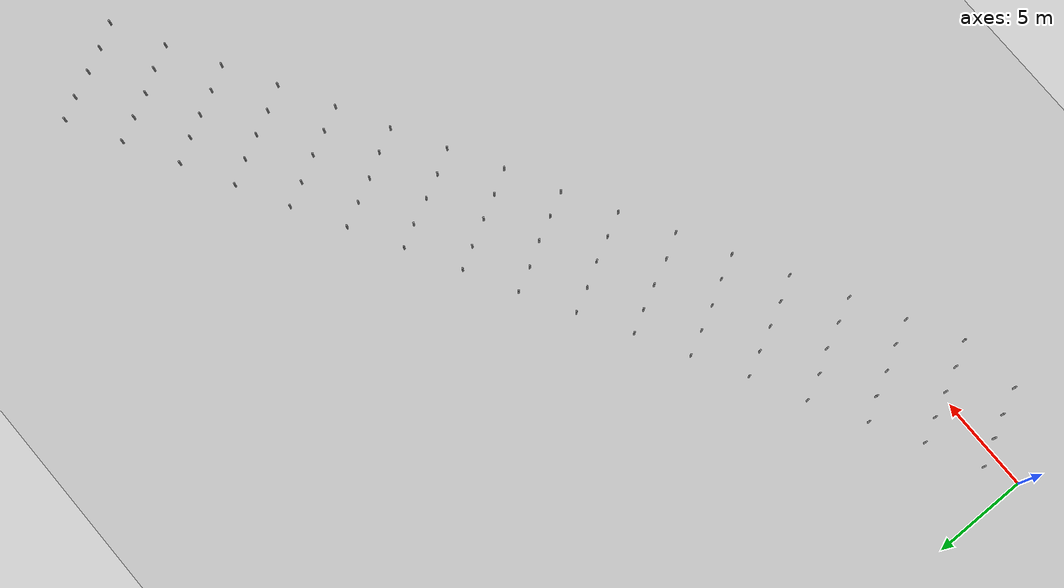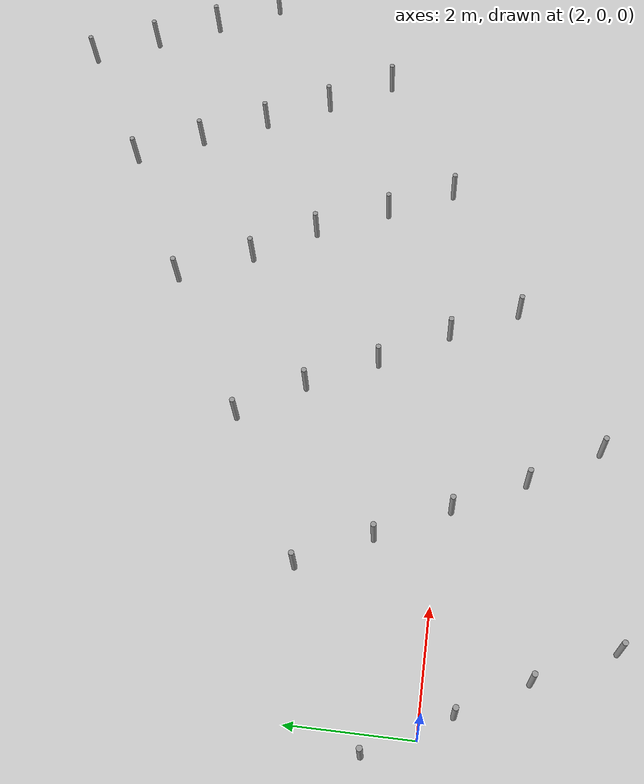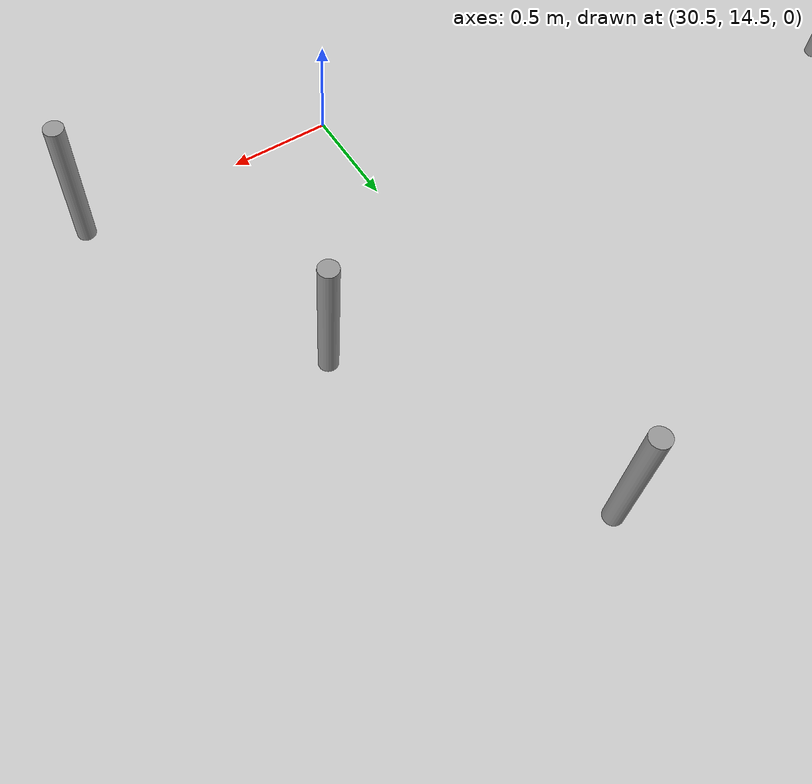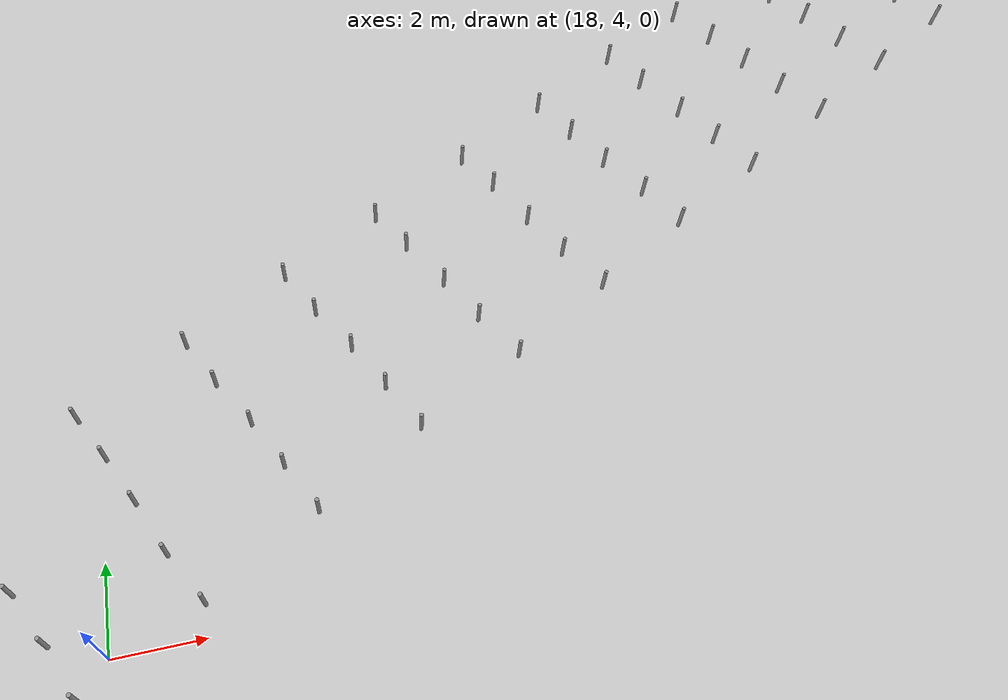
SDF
<?xml version="1.0" encoding="utf-8"?>
<sdf version="1.4">
	<world name="default">
		<model name="unit_cylinder_1">
			<static>0</static>
			<pose>1.7 0.8 0.0 0.0 0.0 0.0</pose>
			<link name="link">
				<kinematic>0</kinematic>
				<inertial>
					<mass>1</mass>
					<inertia>
						<ixz>0</ixz>
						<ixx>1</ixx>
						<ixy>0</ixy>
						<izz>1</izz>
						<iyy>1</iyy>
						<iyz>0</iyz>
					</inertia>
				</inertial>
				<self_collide>0</self_collide>
				<gravity>1</gravity>
				<collision name="collision">
					<geometry>
						<cylinder>
							<length>1.38235</length>
							<radius>0.0456111</radius>
						</cylinder>
					</geometry>
					<max_contacts>10</max_contacts>
					<surface>
						<contact>
							<ode></ode>
						</contact>
						<bounce></bounce>
						<friction>
							<ode></ode>
						</friction>
					</surface>
				</collision>
				<visual name="visual">
					<geometry>
						<cylinder>
							<length>1.38235</length>
							<radius>0.0456111</radius>
						</cylinder>
					</geometry>
					<material>
						<script>
							<uri>file://media/materials/scripts/gazebo.material</uri>
							<name>Gazebo/Grey</name>
						</script>
					</material>
				</visual>
				<velocity_decay>
					<linear>0</linear>
					<angular>0</angular>
				</velocity_decay>
			</link>
		</model>
		<model name="unit_cylinder_1">
			<static>0</static>
			<pose>4.4 2.2 0.0 0.0 0.0 0.0</pose>
			<link name="link">
				<kinematic>0</kinematic>
				<inertial>
					<mass>1</mass>
					<inertia>
						<ixz>0</ixz>
						<ixx>1</ixx>
						<ixy>0</ixy>
						<izz>1</izz>
						<iyy>1</iyy>
						<iyz>0</iyz>
					</inertia>
				</inertial>
				<self_collide>0</self_collide>
				<gravity>1</gravity>
				<collision name="collision">
					<geometry>
						<cylinder>
							<length>1.38235</length>
							<radius>0.0456111</radius>
						</cylinder>
					</geometry>
					<max_contacts>10</max_contacts>
					<surface>
						<contact>
							<ode></ode>
						</contact>
						<bounce></bounce>
						<friction>
							<ode></ode>
						</friction>
					</surface>
				</collision>
				<visual name="visual">
					<geometry>
						<cylinder>
							<length>1.38235</length>
							<radius>0.0456111</radius>
						</cylinder>
					</geometry>
					<material>
						<script>
							<uri>file://media/materials/scripts/gazebo.material</uri>
							<name>Gazebo/Grey</name>
						</script>
					</material>
				</visual>
				<velocity_decay>
					<linear>0</linear>
					<angular>0</angular>
				</velocity_decay>
			</link>
		</model>
		<model name="unit_cylinder_1">
			<static>0</static>
			<pose>6.9 3.6 0.0 0.0 0.0 0.0</pose>
			<link name="link">
				<kinematic>0</kinematic>
				<inertial>
					<mass>1</mass>
					<inertia>
						<ixz>0</ixz>
						<ixx>1</ixx>
						<ixy>0</ixy>
						<izz>1</izz>
						<iyy>1</iyy>
						<iyz>0</iyz>
					</inertia>
				</inertial>
				<self_collide>0</self_collide>
				<gravity>1</gravity>
				<collision name="collision">
					<geometry>
						<cylinder>
							<length>1.38235</length>
							<radius>0.0456111</radius>
						</cylinder>
					</geometry>
					<max_contacts>10</max_contacts>
					<surface>
						<contact>
							<ode></ode>
						</contact>
						<bounce></bounce>
						<friction>
							<ode></ode>
						</friction>
					</surface>
				</collision>
				<visual name="visual">
					<geometry>
						<cylinder>
							<length>1.38235</length>
							<radius>0.0456111</radius>
						</cylinder>
					</geometry>
					<material>
						<script>
							<uri>file://media/materials/scripts/gazebo.material</uri>
							<name>Gazebo/Grey</name>
						</script>
					</material>
				</visual>
				<velocity_decay>
					<linear>0</linear>
					<angular>0</angular>
				</velocity_decay>
			</link>
		</model>
		<model name="unit_cylinder_1">
			<static>0</static>
			<pose>9.6 5.2 0.0 0.0 0.0 0.0</pose>
			<link name="link">
				<kinematic>0</kinematic>
				<inertial>
					<mass>1</mass>
					<inertia>
						<ixz>0</ixz>
						<ixx>1</ixx>
						<ixy>0</ixy>
						<izz>1</izz>
						<iyy>1</iyy>
						<iyz>0</iyz>
					</inertia>
				</inertial>
				<self_collide>0</self_collide>
				<gravity>1</gravity>
				<collision name="collision">
					<geometry>
						<cylinder>
							<length>1.38235</length>
							<radius>0.0456111</radius>
						</cylinder>
					</geometry>
					<max_contacts>10</max_contacts>
					<surface>
						<contact>
							<ode></ode>
						</contact>
						<bounce></bounce>
						<friction>
							<ode></ode>
						</friction>
					</surface>
				</collision>
				<visual name="visual">
					<geometry>
						<cylinder>
							<length>1.38235</length>
							<radius>0.0456111</radius>
						</cylinder>
					</geometry>
					<material>
						<script>
							<uri>file://media/materials/scripts/gazebo.material</uri>
							<name>Gazebo/Grey</name>
						</script>
					</material>
				</visual>
				<velocity_decay>
					<linear>0</linear>
					<angular>0</angular>
				</velocity_decay>
			</link>
		</model>
		<model name="unit_cylinder_1">
			<static>0</static>
			<pose>12.3 6.6 0.0 0.0 0.0 0.0</pose>
			<link name="link">
				<kinematic>0</kinematic>
				<inertial>
					<mass>1</mass>
					<inertia>
						<ixz>0</ixz>
						<ixx>1</ixx>
						<ixy>0</ixy>
						<izz>1</izz>
						<iyy>1</iyy>
						<iyz>0</iyz>
					</inertia>
				</inertial>
				<self_collide>0</self_collide>
				<gravity>1</gravity>
				<collision name="collision">
					<geometry>
						<cylinder>
							<length>1.38235</length>
							<radius>0.0456111</radius>
						</cylinder>
					</geometry>
					<max_contacts>10</max_contacts>
					<surface>
						<contact>
							<ode></ode>
						</contact>
						<bounce></bounce>
						<friction>
							<ode></ode>
						</friction>
					</surface>
				</collision>
				<visual name="visual">
					<geometry>
						<cylinder>
							<length>1.38235</length>
							<radius>0.0456111</radius>
						</cylinder>
					</geometry>
					<material>
						<script>
							<uri>file://media/materials/scripts/gazebo.material</uri>
							<name>Gazebo/Grey</name>
						</script>
					</material>
				</visual>
				<velocity_decay>
					<linear>0</linear>
					<angular>0</angular>
				</velocity_decay>
			</link>
		</model>
		<model name="unit_cylinder_1">
			<static>0</static>
			<pose>14.9 8.1 0.0 0.0 0.0 0.0</pose>
			<link name="link">
				<kinematic>0</kinematic>
				<inertial>
					<mass>1</mass>
					<inertia>
						<ixz>0</ixz>
						<ixx>1</ixx>
						<ixy>0</ixy>
						<izz>1</izz>
						<iyy>1</iyy>
						<iyz>0</iyz>
					</inertia>
				</inertial>
				<self_collide>0</self_collide>
				<gravity>1</gravity>
				<collision name="collision">
					<geometry>
						<cylinder>
							<length>1.38235</length>
							<radius>0.0456111</radius>
						</cylinder>
					</geometry>
					<max_contacts>10</max_contacts>
					<surface>
						<contact>
							<ode></ode>
						</contact>
						<bounce></bounce>
						<friction>
							<ode></ode>
						</friction>
					</surface>
				</collision>
				<visual name="visual">
					<geometry>
						<cylinder>
							<length>1.38235</length>
							<radius>0.0456111</radius>
						</cylinder>
					</geometry>
					<material>
						<script>
							<uri>file://media/materials/scripts/gazebo.material</uri>
							<name>Gazebo/Grey</name>
						</script>
					</material>
				</visual>
				<velocity_decay>
					<linear>0</linear>
					<angular>0</angular>
				</velocity_decay>
			</link>
		</model>
		<model name="unit_cylinder_1">
			<static>0</static>
			<pose>17.5 9.5 0.0 0.0 0.0 0.0</pose>
			<link name="link">
				<kinematic>0</kinematic>
				<inertial>
					<mass>1</mass>
					<inertia>
						<ixz>0</ixz>
						<ixx>1</ixx>
						<ixy>0</ixy>
						<izz>1</izz>
						<iyy>1</iyy>
						<iyz>0</iyz>
					</inertia>
				</inertial>
				<self_collide>0</self_collide>
				<gravity>1</gravity>
				<collision name="collision">
					<geometry>
						<cylinder>
							<length>1.38235</length>
							<radius>0.0456111</radius>
						</cylinder>
					</geometry>
					<max_contacts>10</max_contacts>
					<surface>
						<contact>
							<ode></ode>
						</contact>
						<bounce></bounce>
						<friction>
							<ode></ode>
						</friction>
					</surface>
				</collision>
				<visual name="visual">
					<geometry>
						<cylinder>
							<length>1.38235</length>
							<radius>0.0456111</radius>
						</cylinder>
					</geometry>
					<material>
						<script>
							<uri>file://media/materials/scripts/gazebo.material</uri>
							<name>Gazebo/Grey</name>
						</script>
					</material>
				</visual>
				<velocity_decay>
					<linear>0</linear>
					<angular>0</angular>
				</velocity_decay>
			</link>
		</model>
		<model name="unit_cylinder_1">
			<static>0</static>
			<pose>20.1 11.0 0.0 0.0 0.0 0.0</pose>
			<link name="link">
				<kinematic>0</kinematic>
				<inertial>
					<mass>1</mass>
					<inertia>
						<ixz>0</ixz>
						<ixx>1</ixx>
						<ixy>0</ixy>
						<izz>1</izz>
						<iyy>1</iyy>
						<iyz>0</iyz>
					</inertia>
				</inertial>
				<self_collide>0</self_collide>
				<gravity>1</gravity>
				<collision name="collision">
					<geometry>
						<cylinder>
							<length>1.38235</length>
							<radius>0.0456111</radius>
						</cylinder>
					</geometry>
					<max_contacts>10</max_contacts>
					<surface>
						<contact>
							<ode></ode>
						</contact>
						<bounce></bounce>
						<friction>
							<ode></ode>
						</friction>
					</surface>
				</collision>
				<visual name="visual">
					<geometry>
						<cylinder>
							<length>1.38235</length>
							<radius>0.0456111</radius>
						</cylinder>
					</geometry>
					<material>
						<script>
							<uri>file://media/materials/scripts/gazebo.material</uri>
							<name>Gazebo/Grey</name>
						</script>
					</material>
				</visual>
				<velocity_decay>
					<linear>0</linear>
					<angular>0</angular>
				</velocity_decay>
			</link>
		</model>
		<model name="unit_cylinder_1">
			<static>0</static>
			<pose>22.7 12.5 0.0 0.0 0.0 0.0</pose>
			<link name="link">
				<kinematic>0</kinematic>
				<inertial>
					<mass>1</mass>
					<inertia>
						<ixz>0</ixz>
						<ixx>1</ixx>
						<ixy>0</ixy>
						<izz>1</izz>
						<iyy>1</iyy>
						<iyz>0</iyz>
					</inertia>
				</inertial>
				<self_collide>0</self_collide>
				<gravity>1</gravity>
				<collision name="collision">
					<geometry>
						<cylinder>
							<length>1.38235</length>
							<radius>0.0456111</radius>
						</cylinder>
					</geometry>
					<max_contacts>10</max_contacts>
					<surface>
						<contact>
							<ode></ode>
						</contact>
						<bounce></bounce>
						<friction>
							<ode></ode>
						</friction>
					</surface>
				</collision>
				<visual name="visual">
					<geometry>
						<cylinder>
							<length>1.38235</length>
							<radius>0.0456111</radius>
						</cylinder>
					</geometry>
					<material>
						<script>
							<uri>file://media/materials/scripts/gazebo.material</uri>
							<name>Gazebo/Grey</name>
						</script>
					</material>
				</visual>
				<velocity_decay>
					<linear>0</linear>
					<angular>0</angular>
				</velocity_decay>
			</link>
		</model>
		<model name="unit_cylinder_1">
			<static>0</static>
			<pose>25.3 13.9 0.0 0.0 0.0 0.0</pose>
			<link name="link">
				<kinematic>0</kinematic>
				<inertial>
					<mass>1</mass>
					<inertia>
						<ixz>0</ixz>
						<ixx>1</ixx>
						<ixy>0</ixy>
						<izz>1</izz>
						<iyy>1</iyy>
						<iyz>0</iyz>
					</inertia>
				</inertial>
				<self_collide>0</self_collide>
				<gravity>1</gravity>
				<collision name="collision">
					<geometry>
						<cylinder>
							<length>1.38235</length>
							<radius>0.0456111</radius>
						</cylinder>
					</geometry>
					<max_contacts>10</max_contacts>
					<surface>
						<contact>
							<ode></ode>
						</contact>
						<bounce></bounce>
						<friction>
							<ode></ode>
						</friction>
					</surface>
				</collision>
				<visual name="visual">
					<geometry>
						<cylinder>
							<length>1.38235</length>
							<radius>0.0456111</radius>
						</cylinder>
					</geometry>
					<material>
						<script>
							<uri>file://media/materials/scripts/gazebo.material</uri>
							<name>Gazebo/Grey</name>
						</script>
					</material>
				</visual>
				<velocity_decay>
					<linear>0</linear>
					<angular>0</angular>
				</velocity_decay>
			</link>
		</model>
		<model name="unit_cylinder_1">
			<static>0</static>
			<pose>28.0 15.4 0.0 0.0 0.0 0.0</pose>
			<link name="link">
				<kinematic>0</kinematic>
				<inertial>
					<mass>1</mass>
					<inertia>
						<ixz>0</ixz>
						<ixx>1</ixx>
						<ixy>0</ixy>
						<izz>1</izz>
						<iyy>1</iyy>
						<iyz>0</iyz>
					</inertia>
				</inertial>
				<self_collide>0</self_collide>
				<gravity>1</gravity>
				<collision name="collision">
					<geometry>
						<cylinder>
							<length>1.38235</length>
							<radius>0.0456111</radius>
						</cylinder>
					</geometry>
					<max_contacts>10</max_contacts>
					<surface>
						<contact>
							<ode></ode>
						</contact>
						<bounce></bounce>
						<friction>
							<ode></ode>
						</friction>
					</surface>
				</collision>
				<visual name="visual">
					<geometry>
						<cylinder>
							<length>1.38235</length>
							<radius>0.0456111</radius>
						</cylinder>
					</geometry>
					<material>
						<script>
							<uri>file://media/materials/scripts/gazebo.material</uri>
							<name>Gazebo/Grey</name>
						</script>
					</material>
				</visual>
				<velocity_decay>
					<linear>0</linear>
					<angular>0</angular>
				</velocity_decay>
			</link>
		</model>
		<model name="unit_cylinder_1">
			<static>0</static>
			<pose>30.6 16.9 0.0 0.0 0.0 0.0</pose>
			<link name="link">
				<kinematic>0</kinematic>
				<inertial>
					<mass>1</mass>
					<inertia>
						<ixz>0</ixz>
						<ixx>1</ixx>
						<ixy>0</ixy>
						<izz>1</izz>
						<iyy>1</iyy>
						<iyz>0</iyz>
					</inertia>
				</inertial>
				<self_collide>0</self_collide>
				<gravity>1</gravity>
				<collision name="collision">
					<geometry>
						<cylinder>
							<length>1.38235</length>
							<radius>0.0456111</radius>
						</cylinder>
					</geometry>
					<max_contacts>10</max_contacts>
					<surface>
						<contact>
							<ode></ode>
						</contact>
						<bounce></bounce>
						<friction>
							<ode></ode>
						</friction>
					</surface>
				</collision>
				<visual name="visual">
					<geometry>
						<cylinder>
							<length>1.38235</length>
							<radius>0.0456111</radius>
						</cylinder>
					</geometry>
					<material>
						<script>
							<uri>file://media/materials/scripts/gazebo.material</uri>
							<name>Gazebo/Grey</name>
						</script>
					</material>
				</visual>
				<velocity_decay>
					<linear>0</linear>
					<angular>0</angular>
				</velocity_decay>
			</link>
		</model>
		<model name="unit_cylinder_1">
			<static>0</static>
			<pose>33.2 18.4 0.0 0.0 0.0 0.0</pose>
			<link name="link">
				<kinematic>0</kinematic>
				<inertial>
					<mass>1</mass>
					<inertia>
						<ixz>0</ixz>
						<ixx>1</ixx>
						<ixy>0</ixy>
						<izz>1</izz>
						<iyy>1</iyy>
						<iyz>0</iyz>
					</inertia>
				</inertial>
				<self_collide>0</self_collide>
				<gravity>1</gravity>
				<collision name="collision">
					<geometry>
						<cylinder>
							<length>1.38235</length>
							<radius>0.0456111</radius>
						</cylinder>
					</geometry>
					<max_contacts>10</max_contacts>
					<surface>
						<contact>
							<ode></ode>
						</contact>
						<bounce></bounce>
						<friction>
							<ode></ode>
						</friction>
					</surface>
				</collision>
				<visual name="visual">
					<geometry>
						<cylinder>
							<length>1.38235</length>
							<radius>0.0456111</radius>
						</cylinder>
					</geometry>
					<material>
						<script>
							<uri>file://media/materials/scripts/gazebo.material</uri>
							<name>Gazebo/Grey</name>
						</script>
					</material>
				</visual>
				<velocity_decay>
					<linear>0</linear>
					<angular>0</angular>
				</velocity_decay>
			</link>
		</model>
		<model name="unit_cylinder_1">
			<static>0</static>
			<pose>35.8 19.8 0.0 0.0 0.0 0.0</pose>
			<link name="link">
				<kinematic>0</kinematic>
				<inertial>
					<mass>1</mass>
					<inertia>
						<ixz>0</ixz>
						<ixx>1</ixx>
						<ixy>0</ixy>
						<izz>1</izz>
						<iyy>1</iyy>
						<iyz>0</iyz>
					</inertia>
				</inertial>
				<self_collide>0</self_collide>
				<gravity>1</gravity>
				<collision name="collision">
					<geometry>
						<cylinder>
							<length>1.38235</length>
							<radius>0.0456111</radius>
						</cylinder>
					</geometry>
					<max_contacts>10</max_contacts>
					<surface>
						<contact>
							<ode></ode>
						</contact>
						<bounce></bounce>
						<friction>
							<ode></ode>
						</friction>
					</surface>
				</collision>
				<visual name="visual">
					<geometry>
						<cylinder>
							<length>1.38235</length>
							<radius>0.0456111</radius>
						</cylinder>
					</geometry>
					<material>
						<script>
							<uri>file://media/materials/scripts/gazebo.material</uri>
							<name>Gazebo/Grey</name>
						</script>
					</material>
				</visual>
				<velocity_decay>
					<linear>0</linear>
					<angular>0</angular>
				</velocity_decay>
			</link>
		</model>
		<model name="unit_cylinder_1">
			<static>0</static>
			<pose>38.4 21.2 0.0 0.0 0.0 0.0</pose>
			<link name="link">
				<kinematic>0</kinematic>
				<inertial>
					<mass>1</mass>
					<inertia>
						<ixz>0</ixz>
						<ixx>1</ixx>
						<ixy>0</ixy>
						<izz>1</izz>
						<iyy>1</iyy>
						<iyz>0</iyz>
					</inertia>
				</inertial>
				<self_collide>0</self_collide>
				<gravity>1</gravity>
				<collision name="collision">
					<geometry>
						<cylinder>
							<length>1.38235</length>
							<radius>0.0456111</radius>
						</cylinder>
					</geometry>
					<max_contacts>10</max_contacts>
					<surface>
						<contact>
							<ode></ode>
						</contact>
						<bounce></bounce>
						<friction>
							<ode></ode>
						</friction>
					</surface>
				</collision>
				<visual name="visual">
					<geometry>
						<cylinder>
							<length>1.38235</length>
							<radius>0.0456111</radius>
						</cylinder>
					</geometry>
					<material>
						<script>
							<uri>file://media/materials/scripts/gazebo.material</uri>
							<name>Gazebo/Grey</name>
						</script>
					</material>
				</visual>
				<velocity_decay>
					<linear>0</linear>
					<angular>0</angular>
				</velocity_decay>
			</link>
		</model>
		<model name="unit_cylinder_1">
			<static>0</static>
			<pose>41.1 22.7 0.0 0.0 0.0 0.0</pose>
			<link name="link">
				<kinematic>0</kinematic>
				<inertial>
					<mass>1</mass>
					<inertia>
						<ixz>0</ixz>
						<ixx>1</ixx>
						<ixy>0</ixy>
						<izz>1</izz>
						<iyy>1</iyy>
						<iyz>0</iyz>
					</inertia>
				</inertial>
				<self_collide>0</self_collide>
				<gravity>1</gravity>
				<collision name="collision">
					<geometry>
						<cylinder>
							<length>1.38235</length>
							<radius>0.0456111</radius>
						</cylinder>
					</geometry>
					<max_contacts>10</max_contacts>
					<surface>
						<contact>
							<ode></ode>
						</contact>
						<bounce></bounce>
						<friction>
							<ode></ode>
						</friction>
					</surface>
				</collision>
				<visual name="visual">
					<geometry>
						<cylinder>
							<length>1.38235</length>
							<radius>0.0456111</radius>
						</cylinder>
					</geometry>
					<material>
						<script>
							<uri>file://media/materials/scripts/gazebo.material</uri>
							<name>Gazebo/Grey</name>
						</script>
					</material>
				</visual>
				<velocity_decay>
					<linear>0</linear>
					<angular>0</angular>
				</velocity_decay>
			</link>
		</model>
		<model name="unit_cylinder_1">
			<static>0</static>
			<pose>43.8 24.2 0.0 0.0 0.0 0.0</pose>
			<link name="link">
				<kinematic>0</kinematic>
				<inertial>
					<mass>1</mass>
					<inertia>
						<ixz>0</ixz>
						<ixx>1</ixx>
						<ixy>0</ixy>
						<izz>1</izz>
						<iyy>1</iyy>
						<iyz>0</iyz>
					</inertia>
				</inertial>
				<self_collide>0</self_collide>
				<gravity>1</gravity>
				<collision name="collision">
					<geometry>
						<cylinder>
							<length>1.38235</length>
							<radius>0.0456111</radius>
						</cylinder>
					</geometry>
					<max_contacts>10</max_contacts>
					<surface>
						<contact>
							<ode></ode>
						</contact>
						<bounce></bounce>
						<friction>
							<ode></ode>
						</friction>
					</surface>
				</collision>
				<visual name="visual">
					<geometry>
						<cylinder>
							<length>1.38235</length>
							<radius>0.0456111</radius>
						</cylinder>
					</geometry>
					<material>
						<script>
							<uri>file://media/materials/scripts/gazebo.material</uri>
							<name>Gazebo/Grey</name>
						</script>
					</material>
				</visual>
				<velocity_decay>
					<linear>0</linear>
					<angular>0</angular>
				</velocity_decay>
			</link>
		</model>
		<model name="unit_cylinder_1">
			<static>0</static>
			<pose>44.4 23.1 0.0 0.0 0.0 0.0</pose>
			<link name="link">
				<kinematic>0</kinematic>
				<inertial>
					<mass>1</mass>
					<inertia>
						<ixz>0</ixz>
						<ixx>1</ixx>
						<ixy>0</ixy>
						<izz>1</izz>
						<iyy>1</iyy>
						<iyz>0</iyz>
					</inertia>
				</inertial>
				<self_collide>0</self_collide>
				<gravity>1</gravity>
				<collision name="collision">
					<geometry>
						<cylinder>
							<length>1.38235</length>
							<radius>0.0456111</radius>
						</cylinder>
					</geometry>
					<max_contacts>10</max_contacts>
					<surface>
						<contact>
							<ode></ode>
						</contact>
						<bounce></bounce>
						<friction>
							<ode></ode>
						</friction>
					</surface>
				</collision>
				<visual name="visual">
					<geometry>
						<cylinder>
							<length>1.38235</length>
							<radius>0.0456111</radius>
						</cylinder>
					</geometry>
					<material>
						<script>
							<uri>file://media/materials/scripts/gazebo.material</uri>
							<name>Gazebo/Grey</name>
						</script>
					</material>
				</visual>
				<velocity_decay>
					<linear>0</linear>
					<angular>0</angular>
				</velocity_decay>
			</link>
		</model>
		<model name="unit_cylinder_1">
			<static>0</static>
			<pose>41.7 21.5 0.0 0.0 0.0 0.0</pose>
			<link name="link">
				<kinematic>0</kinematic>
				<inertial>
					<mass>1</mass>
					<inertia>
						<ixz>0</ixz>
						<ixx>1</ixx>
						<ixy>0</ixy>
						<izz>1</izz>
						<iyy>1</iyy>
						<iyz>0</iyz>
					</inertia>
				</inertial>
				<self_collide>0</self_collide>
				<gravity>1</gravity>
				<collision name="collision">
					<geometry>
						<cylinder>
							<length>1.38235</length>
							<radius>0.0456111</radius>
						</cylinder>
					</geometry>
					<max_contacts>10</max_contacts>
					<surface>
						<contact>
							<ode></ode>
						</contact>
						<bounce></bounce>
						<friction>
							<ode></ode>
						</friction>
					</surface>
				</collision>
				<visual name="visual">
					<geometry>
						<cylinder>
							<length>1.38235</length>
							<radius>0.0456111</radius>
						</cylinder>
					</geometry>
					<material>
						<script>
							<uri>file://media/materials/scripts/gazebo.material</uri>
							<name>Gazebo/Grey</name>
						</script>
					</material>
				</visual>
				<velocity_decay>
					<linear>0</linear>
					<angular>0</angular>
				</velocity_decay>
			</link>
		</model>
		<model name="unit_cylinder_1">
			<static>0</static>
			<pose>39.1 20.0 0.0 0.0 0.0 0.0</pose>
			<link name="link">
				<kinematic>0</kinematic>
				<inertial>
					<mass>1</mass>
					<inertia>
						<ixz>0</ixz>
						<ixx>1</ixx>
						<ixy>0</ixy>
						<izz>1</izz>
						<iyy>1</iyy>
						<iyz>0</iyz>
					</inertia>
				</inertial>
				<self_collide>0</self_collide>
				<gravity>1</gravity>
				<collision name="collision">
					<geometry>
						<cylinder>
							<length>1.38235</length>
							<radius>0.0456111</radius>
						</cylinder>
					</geometry>
					<max_contacts>10</max_contacts>
					<surface>
						<contact>
							<ode></ode>
						</contact>
						<bounce></bounce>
						<friction>
							<ode></ode>
						</friction>
					</surface>
				</collision>
				<visual name="visual">
					<geometry>
						<cylinder>
							<length>1.38235</length>
							<radius>0.0456111</radius>
						</cylinder>
					</geometry>
					<material>
						<script>
							<uri>file://media/materials/scripts/gazebo.material</uri>
							<name>Gazebo/Grey</name>
						</script>
					</material>
				</visual>
				<velocity_decay>
					<linear>0</linear>
					<angular>0</angular>
				</velocity_decay>
			</link>
		</model>
		<model name="unit_cylinder_1">
			<static>0</static>
			<pose>36.5 18.6 0.0 0.0 0.0 0.0</pose>
			<link name="link">
				<kinematic>0</kinematic>
				<inertial>
					<mass>1</mass>
					<inertia>
						<ixz>0</ixz>
						<ixx>1</ixx>
						<ixy>0</ixy>
						<izz>1</izz>
						<iyy>1</iyy>
						<iyz>0</iyz>
					</inertia>
				</inertial>
				<self_collide>0</self_collide>
				<gravity>1</gravity>
				<collision name="collision">
					<geometry>
						<cylinder>
							<length>1.38235</length>
							<radius>0.0456111</radius>
						</cylinder>
					</geometry>
					<max_contacts>10</max_contacts>
					<surface>
						<contact>
							<ode></ode>
						</contact>
						<bounce></bounce>
						<friction>
							<ode></ode>
						</friction>
					</surface>
				</collision>
				<visual name="visual">
					<geometry>
						<cylinder>
							<length>1.38235</length>
							<radius>0.0456111</radius>
						</cylinder>
					</geometry>
					<material>
						<script>
							<uri>file://media/materials/scripts/gazebo.material</uri>
							<name>Gazebo/Grey</name>
						</script>
					</material>
				</visual>
				<velocity_decay>
					<linear>0</linear>
					<angular>0</angular>
				</velocity_decay>
			</link>
		</model>
		<model name="unit_cylinder_1">
			<static>0</static>
			<pose>33.8 17.2 0.0 0.0 0.0 0.0</pose>
			<link name="link">
				<kinematic>0</kinematic>
				<inertial>
					<mass>1</mass>
					<inertia>
						<ixz>0</ixz>
						<ixx>1</ixx>
						<ixy>0</ixy>
						<izz>1</izz>
						<iyy>1</iyy>
						<iyz>0</iyz>
					</inertia>
				</inertial>
				<self_collide>0</self_collide>
				<gravity>1</gravity>
				<collision name="collision">
					<geometry>
						<cylinder>
							<length>1.38235</length>
							<radius>0.0456111</radius>
						</cylinder>
					</geometry>
					<max_contacts>10</max_contacts>
					<surface>
						<contact>
							<ode></ode>
						</contact>
						<bounce></bounce>
						<friction>
							<ode></ode>
						</friction>
					</surface>
				</collision>
				<visual name="visual">
					<geometry>
						<cylinder>
							<length>1.38235</length>
							<radius>0.0456111</radius>
						</cylinder>
					</geometry>
					<material>
						<script>
							<uri>file://media/materials/scripts/gazebo.material</uri>
							<name>Gazebo/Grey</name>
						</script>
					</material>
				</visual>
				<velocity_decay>
					<linear>0</linear>
					<angular>0</angular>
				</velocity_decay>
			</link>
		</model>
		<model name="unit_cylinder_1">
			<static>0</static>
			<pose>31.2 15.7 0.0 0.0 0.0 0.0</pose>
			<link name="link">
				<kinematic>0</kinematic>
				<inertial>
					<mass>1</mass>
					<inertia>
						<ixz>0</ixz>
						<ixx>1</ixx>
						<ixy>0</ixy>
						<izz>1</izz>
						<iyy>1</iyy>
						<iyz>0</iyz>
					</inertia>
				</inertial>
				<self_collide>0</self_collide>
				<gravity>1</gravity>
				<collision name="collision">
					<geometry>
						<cylinder>
							<length>1.38235</length>
							<radius>0.0456111</radius>
						</cylinder>
					</geometry>
					<max_contacts>10</max_contacts>
					<surface>
						<contact>
							<ode></ode>
						</contact>
						<bounce></bounce>
						<friction>
							<ode></ode>
						</friction>
					</surface>
				</collision>
				<visual name="visual">
					<geometry>
						<cylinder>
							<length>1.38235</length>
							<radius>0.0456111</radius>
						</cylinder>
					</geometry>
					<material>
						<script>
							<uri>file://media/materials/scripts/gazebo.material</uri>
							<name>Gazebo/Grey</name>
						</script>
					</material>
				</visual>
				<velocity_decay>
					<linear>0</linear>
					<angular>0</angular>
				</velocity_decay>
			</link>
		</model>
		<model name="unit_cylinder_1">
			<static>0</static>
			<pose>28.6 14.3 0.0 0.0 0.0 0.0</pose>
			<link name="link">
				<kinematic>0</kinematic>
				<inertial>
					<mass>1</mass>
					<inertia>
						<ixz>0</ixz>
						<ixx>1</ixx>
						<ixy>0</ixy>
						<izz>1</izz>
						<iyy>1</iyy>
						<iyz>0</iyz>
					</inertia>
				</inertial>
				<self_collide>0</self_collide>
				<gravity>1</gravity>
				<collision name="collision">
					<geometry>
						<cylinder>
							<length>1.38235</length>
							<radius>0.0456111</radius>
						</cylinder>
					</geometry>
					<max_contacts>10</max_contacts>
					<surface>
						<contact>
							<ode></ode>
						</contact>
						<bounce></bounce>
						<friction>
							<ode></ode>
						</friction>
					</surface>
				</collision>
				<visual name="visual">
					<geometry>
						<cylinder>
							<length>1.38235</length>
							<radius>0.0456111</radius>
						</cylinder>
					</geometry>
					<material>
						<script>
							<uri>file://media/materials/scripts/gazebo.material</uri>
							<name>Gazebo/Grey</name>
						</script>
					</material>
				</visual>
				<velocity_decay>
					<linear>0</linear>
					<angular>0</angular>
				</velocity_decay>
			</link>
		</model>
		<model name="unit_cylinder_1">
			<static>0</static>
			<pose>25.9 12.8 0.0 0.0 0.0 0.0</pose>
			<link name="link">
				<kinematic>0</kinematic>
				<inertial>
					<mass>1</mass>
					<inertia>
						<ixz>0</ixz>
						<ixx>1</ixx>
						<ixy>0</ixy>
						<izz>1</izz>
						<iyy>1</iyy>
						<iyz>0</iyz>
					</inertia>
				</inertial>
				<self_collide>0</self_collide>
				<gravity>1</gravity>
				<collision name="collision">
					<geometry>
						<cylinder>
							<length>1.38235</length>
							<radius>0.0456111</radius>
						</cylinder>
					</geometry>
					<max_contacts>10</max_contacts>
					<surface>
						<contact>
							<ode></ode>
						</contact>
						<bounce></bounce>
						<friction>
							<ode></ode>
						</friction>
					</surface>
				</collision>
				<visual name="visual">
					<geometry>
						<cylinder>
							<length>1.38235</length>
							<radius>0.0456111</radius>
						</cylinder>
					</geometry>
					<material>
						<script>
							<uri>file://media/materials/scripts/gazebo.material</uri>
							<name>Gazebo/Grey</name>
						</script>
					</material>
				</visual>
				<velocity_decay>
					<linear>0</linear>
					<angular>0</angular>
				</velocity_decay>
			</link>
		</model>
		<model name="unit_cylinder_1">
			<static>0</static>
			<pose>23.3 11.3 0.0 0.0 0.0 0.0</pose>
			<link name="link">
				<kinematic>0</kinematic>
				<inertial>
					<mass>1</mass>
					<inertia>
						<ixz>0</ixz>
						<ixx>1</ixx>
						<ixy>0</ixy>
						<izz>1</izz>
						<iyy>1</iyy>
						<iyz>0</iyz>
					</inertia>
				</inertial>
				<self_collide>0</self_collide>
				<gravity>1</gravity>
				<collision name="collision">
					<geometry>
						<cylinder>
							<length>1.38235</length>
							<radius>0.0456111</radius>
						</cylinder>
					</geometry>
					<max_contacts>10</max_contacts>
					<surface>
						<contact>
							<ode></ode>
						</contact>
						<bounce></bounce>
						<friction>
							<ode></ode>
						</friction>
					</surface>
				</collision>
				<visual name="visual">
					<geometry>
						<cylinder>
							<length>1.38235</length>
							<radius>0.0456111</radius>
						</cylinder>
					</geometry>
					<material>
						<script>
							<uri>file://media/materials/scripts/gazebo.material</uri>
							<name>Gazebo/Grey</name>
						</script>
					</material>
				</visual>
				<velocity_decay>
					<linear>0</linear>
					<angular>0</angular>
				</velocity_decay>
			</link>
		</model>
		<model name="unit_cylinder_1">
			<static>0</static>
			<pose>20.7 9.8 0.0 0.0 0.0 0.0</pose>
			<link name="link">
				<kinematic>0</kinematic>
				<inertial>
					<mass>1</mass>
					<inertia>
						<ixz>0</ixz>
						<ixx>1</ixx>
						<ixy>0</ixy>
						<izz>1</izz>
						<iyy>1</iyy>
						<iyz>0</iyz>
					</inertia>
				</inertial>
				<self_collide>0</self_collide>
				<gravity>1</gravity>
				<collision name="collision">
					<geometry>
						<cylinder>
							<length>1.38235</length>
							<radius>0.0456111</radius>
						</cylinder>
					</geometry>
					<max_contacts>10</max_contacts>
					<surface>
						<contact>
							<ode></ode>
						</contact>
						<bounce></bounce>
						<friction>
							<ode></ode>
						</friction>
					</surface>
				</collision>
				<visual name="visual">
					<geometry>
						<cylinder>
							<length>1.38235</length>
							<radius>0.0456111</radius>
						</cylinder>
					</geometry>
					<material>
						<script>
							<uri>file://media/materials/scripts/gazebo.material</uri>
							<name>Gazebo/Grey</name>
						</script>
					</material>
				</visual>
				<velocity_decay>
					<linear>0</linear>
					<angular>0</angular>
				</velocity_decay>
			</link>
		</model>
		<model name="unit_cylinder_1">
			<static>0</static>
			<pose>18.1 8.4 0.0 0.0 0.0 0.0</pose>
			<link name="link">
				<kinematic>0</kinematic>
				<inertial>
					<mass>1</mass>
					<inertia>
						<ixz>0</ixz>
						<ixx>1</ixx>
						<ixy>0</ixy>
						<izz>1</izz>
						<iyy>1</iyy>
						<iyz>0</iyz>
					</inertia>
				</inertial>
				<self_collide>0</self_collide>
				<gravity>1</gravity>
				<collision name="collision">
					<geometry>
						<cylinder>
							<length>1.38235</length>
							<radius>0.0456111</radius>
						</cylinder>
					</geometry>
					<max_contacts>10</max_contacts>
					<surface>
						<contact>
							<ode></ode>
						</contact>
						<bounce></bounce>
						<friction>
							<ode></ode>
						</friction>
					</surface>
				</collision>
				<visual name="visual">
					<geometry>
						<cylinder>
							<length>1.38235</length>
							<radius>0.0456111</radius>
						</cylinder>
					</geometry>
					<material>
						<script>
							<uri>file://media/materials/scripts/gazebo.material</uri>
							<name>Gazebo/Grey</name>
						</script>
					</material>
				</visual>
				<velocity_decay>
					<linear>0</linear>
					<angular>0</angular>
				</velocity_decay>
			</link>
		</model>
		<model name="unit_cylinder_1">
			<static>0</static>
			<pose>15.5 6.9 0.0 0.0 0.0 0.0</pose>
			<link name="link">
				<kinematic>0</kinematic>
				<inertial>
					<mass>1</mass>
					<inertia>
						<ixz>0</ixz>
						<ixx>1</ixx>
						<ixy>0</ixy>
						<izz>1</izz>
						<iyy>1</iyy>
						<iyz>0</iyz>
					</inertia>
				</inertial>
				<self_collide>0</self_collide>
				<gravity>1</gravity>
				<collision name="collision">
					<geometry>
						<cylinder>
							<length>1.38235</length>
							<radius>0.0456111</radius>
						</cylinder>
					</geometry>
					<max_contacts>10</max_contacts>
					<surface>
						<contact>
							<ode></ode>
						</contact>
						<bounce></bounce>
						<friction>
							<ode></ode>
						</friction>
					</surface>
				</collision>
				<visual name="visual">
					<geometry>
						<cylinder>
							<length>1.38235</length>
							<radius>0.0456111</radius>
						</cylinder>
					</geometry>
					<material>
						<script>
							<uri>file://media/materials/scripts/gazebo.material</uri>
							<name>Gazebo/Grey</name>
						</script>
					</material>
				</visual>
				<velocity_decay>
					<linear>0</linear>
					<angular>0</angular>
				</velocity_decay>
			</link>
		</model>
		<model name="unit_cylinder_1">
			<static>0</static>
			<pose>12.9 5.4 0.0 0.0 0.0 0.0</pose>
			<link name="link">
				<kinematic>0</kinematic>
				<inertial>
					<mass>1</mass>
					<inertia>
						<ixz>0</ixz>
						<ixx>1</ixx>
						<ixy>0</ixy>
						<izz>1</izz>
						<iyy>1</iyy>
						<iyz>0</iyz>
					</inertia>
				</inertial>
				<self_collide>0</self_collide>
				<gravity>1</gravity>
				<collision name="collision">
					<geometry>
						<cylinder>
							<length>1.38235</length>
							<radius>0.0456111</radius>
						</cylinder>
					</geometry>
					<max_contacts>10</max_contacts>
					<surface>
						<contact>
							<ode></ode>
						</contact>
						<bounce></bounce>
						<friction>
							<ode></ode>
						</friction>
					</surface>
				</collision>
				<visual name="visual">
					<geometry>
						<cylinder>
							<length>1.38235</length>
							<radius>0.0456111</radius>
						</cylinder>
					</geometry>
					<material>
						<script>
							<uri>file://media/materials/scripts/gazebo.material</uri>
							<name>Gazebo/Grey</name>
						</script>
					</material>
				</visual>
				<velocity_decay>
					<linear>0</linear>
					<angular>0</angular>
				</velocity_decay>
			</link>
		</model>
		<model name="unit_cylinder_1">
			<static>0</static>
			<pose>10.2 3.9 0.0 0.0 0.0 0.0</pose>
			<link name="link">
				<kinematic>0</kinematic>
				<inertial>
					<mass>1</mass>
					<inertia>
						<ixz>0</ixz>
						<ixx>1</ixx>
						<ixy>0</ixy>
						<izz>1</izz>
						<iyy>1</iyy>
						<iyz>0</iyz>
					</inertia>
				</inertial>
				<self_collide>0</self_collide>
				<gravity>1</gravity>
				<collision name="collision">
					<geometry>
						<cylinder>
							<length>1.38235</length>
							<radius>0.0456111</radius>
						</cylinder>
					</geometry>
					<max_contacts>10</max_contacts>
					<surface>
						<contact>
							<ode></ode>
						</contact>
						<bounce></bounce>
						<friction>
							<ode></ode>
						</friction>
					</surface>
				</collision>
				<visual name="visual">
					<geometry>
						<cylinder>
							<length>1.38235</length>
							<radius>0.0456111</radius>
						</cylinder>
					</geometry>
					<material>
						<script>
							<uri>file://media/materials/scripts/gazebo.material</uri>
							<name>Gazebo/Grey</name>
						</script>
					</material>
				</visual>
				<velocity_decay>
					<linear>0</linear>
					<angular>0</angular>
				</velocity_decay>
			</link>
		</model>
		<model name="unit_cylinder_1">
			<static>0</static>
			<pose>7.6 2.5 0.0 0.0 0.0 0.0</pose>
			<link name="link">
				<kinematic>0</kinematic>
				<inertial>
					<mass>1</mass>
					<inertia>
						<ixz>0</ixz>
						<ixx>1</ixx>
						<ixy>0</ixy>
						<izz>1</izz>
						<iyy>1</iyy>
						<iyz>0</iyz>
					</inertia>
				</inertial>
				<self_collide>0</self_collide>
				<gravity>1</gravity>
				<collision name="collision">
					<geometry>
						<cylinder>
							<length>1.38235</length>
							<radius>0.0456111</radius>
						</cylinder>
					</geometry>
					<max_contacts>10</max_contacts>
					<surface>
						<contact>
							<ode></ode>
						</contact>
						<bounce></bounce>
						<friction>
							<ode></ode>
						</friction>
					</surface>
				</collision>
				<visual name="visual">
					<geometry>
						<cylinder>
							<length>1.38235</length>
							<radius>0.0456111</radius>
						</cylinder>
					</geometry>
					<material>
						<script>
							<uri>file://media/materials/scripts/gazebo.material</uri>
							<name>Gazebo/Grey</name>
						</script>
					</material>
				</visual>
				<velocity_decay>
					<linear>0</linear>
					<angular>0</angular>
				</velocity_decay>
			</link>
		</model>
		<model name="unit_cylinder_1">
			<static>0</static>
			<pose>5.0 1.0 0.0 0.0 0.0 0.0</pose>
			<link name="link">
				<kinematic>0</kinematic>
				<inertial>
					<mass>1</mass>
					<inertia>
						<ixz>0</ixz>
						<ixx>1</ixx>
						<ixy>0</ixy>
						<izz>1</izz>
						<iyy>1</iyy>
						<iyz>0</iyz>
					</inertia>
				</inertial>
				<self_collide>0</self_collide>
				<gravity>1</gravity>
				<collision name="collision">
					<geometry>
						<cylinder>
							<length>1.38235</length>
							<radius>0.0456111</radius>
						</cylinder>
					</geometry>
					<max_contacts>10</max_contacts>
					<surface>
						<contact>
							<ode></ode>
						</contact>
						<bounce></bounce>
						<friction>
							<ode></ode>
						</friction>
					</surface>
				</collision>
				<visual name="visual">
					<geometry>
						<cylinder>
							<length>1.38235</length>
							<radius>0.0456111</radius>
						</cylinder>
					</geometry>
					<material>
						<script>
							<uri>file://media/materials/scripts/gazebo.material</uri>
							<name>Gazebo/Grey</name>
						</script>
					</material>
				</visual>
				<velocity_decay>
					<linear>0</linear>
					<angular>0</angular>
				</velocity_decay>
			</link>
		</model>
		<model name="unit_cylinder_1">
			<static>0</static>
			<pose>2.4 -0.5 0.0 0.0 0.0 0.0</pose>
			<link name="link">
				<kinematic>0</kinematic>
				<inertial>
					<mass>1</mass>
					<inertia>
						<ixz>0</ixz>
						<ixx>1</ixx>
						<ixy>0</ixy>
						<izz>1</izz>
						<iyy>1</iyy>
						<iyz>0</iyz>
					</inertia>
				</inertial>
				<self_collide>0</self_collide>
				<gravity>1</gravity>
				<collision name="collision">
					<geometry>
						<cylinder>
							<length>1.38235</length>
							<radius>0.0456111</radius>
						</cylinder>
					</geometry>
					<max_contacts>10</max_contacts>
					<surface>
						<contact>
							<ode></ode>
						</contact>
						<bounce></bounce>
						<friction>
							<ode></ode>
						</friction>
					</surface>
				</collision>
				<visual name="visual">
					<geometry>
						<cylinder>
							<length>1.38235</length>
							<radius>0.0456111</radius>
						</cylinder>
					</geometry>
					<material>
						<script>
							<uri>file://media/materials/scripts/gazebo.material</uri>
							<name>Gazebo/Grey</name>
						</script>
					</material>
				</visual>
				<velocity_decay>
					<linear>0</linear>
					<angular>0</angular>
				</velocity_decay>
			</link>
		</model>
		<model name="unit_cylinder_1">
			<static>0</static>
			<pose>3.0 -1.6 0.0 0.0 0.0 0.0</pose>
			<link name="link">
				<kinematic>0</kinematic>
				<inertial>
					<mass>1</mass>
					<inertia>
						<ixz>0</ixz>
						<ixx>1</ixx>
						<ixy>0</ixy>
						<izz>1</izz>
						<iyy>1</iyy>
						<iyz>0</iyz>
					</inertia>
				</inertial>
				<self_collide>0</self_collide>
				<gravity>1</gravity>
				<collision name="collision">
					<geometry>
						<cylinder>
							<length>1.38235</length>
							<radius>0.0456111</radius>
						</cylinder>
					</geometry>
					<max_contacts>10</max_contacts>
					<surface>
						<contact>
							<ode></ode>
						</contact>
						<bounce></bounce>
						<friction>
							<ode></ode>
						</friction>
					</surface>
				</collision>
				<visual name="visual">
					<geometry>
						<cylinder>
							<length>1.38235</length>
							<radius>0.0456111</radius>
						</cylinder>
					</geometry>
					<material>
						<script>
							<uri>file://media/materials/scripts/gazebo.material</uri>
							<name>Gazebo/Grey</name>
						</script>
					</material>
				</visual>
				<velocity_decay>
					<linear>0</linear>
					<angular>0</angular>
				</velocity_decay>
			</link>
		</model>
		<model name="unit_cylinder_1">
			<static>0</static>
			<pose>5.6 -0.2 0.0 0.0 0.0 0.0</pose>
			<link name="link">
				<kinematic>0</kinematic>
				<inertial>
					<mass>1</mass>
					<inertia>
						<ixz>0</ixz>
						<ixx>1</ixx>
						<ixy>0</ixy>
						<izz>1</izz>
						<iyy>1</iyy>
						<iyz>0</iyz>
					</inertia>
				</inertial>
				<self_collide>0</self_collide>
				<gravity>1</gravity>
				<collision name="collision">
					<geometry>
						<cylinder>
							<length>1.38235</length>
							<radius>0.0456111</radius>
						</cylinder>
					</geometry>
					<max_contacts>10</max_contacts>
					<surface>
						<contact>
							<ode></ode>
						</contact>
						<bounce></bounce>
						<friction>
							<ode></ode>
						</friction>
					</surface>
				</collision>
				<visual name="visual">
					<geometry>
						<cylinder>
							<length>1.38235</length>
							<radius>0.0456111</radius>
						</cylinder>
					</geometry>
					<material>
						<script>
							<uri>file://media/materials/scripts/gazebo.material</uri>
							<name>Gazebo/Grey</name>
						</script>
					</material>
				</visual>
				<velocity_decay>
					<linear>0</linear>
					<angular>0</angular>
				</velocity_decay>
			</link>
		</model>
		<model name="unit_cylinder_1">
			<static>0</static>
			<pose>8.2 1.3 0.0 0.0 0.0 0.0</pose>
			<link name="link">
				<kinematic>0</kinematic>
				<inertial>
					<mass>1</mass>
					<inertia>
						<ixz>0</ixz>
						<ixx>1</ixx>
						<ixy>0</ixy>
						<izz>1</izz>
						<iyy>1</iyy>
						<iyz>0</iyz>
					</inertia>
				</inertial>
				<self_collide>0</self_collide>
				<gravity>1</gravity>
				<collision name="collision">
					<geometry>
						<cylinder>
							<length>1.38235</length>
							<radius>0.0456111</radius>
						</cylinder>
					</geometry>
					<max_contacts>10</max_contacts>
					<surface>
						<contact>
							<ode></ode>
						</contact>
						<bounce></bounce>
						<friction>
							<ode></ode>
						</friction>
					</surface>
				</collision>
				<visual name="visual">
					<geometry>
						<cylinder>
							<length>1.38235</length>
							<radius>0.0456111</radius>
						</cylinder>
					</geometry>
					<material>
						<script>
							<uri>file://media/materials/scripts/gazebo.material</uri>
							<name>Gazebo/Grey</name>
						</script>
					</material>
				</visual>
				<velocity_decay>
					<linear>0</linear>
					<angular>0</angular>
				</velocity_decay>
			</link>
		</model>
		<model name="unit_cylinder_1">
			<static>0</static>
			<pose>10.9 2.8 0.0 0.0 0.0 0.0</pose>
			<link name="link">
				<kinematic>0</kinematic>
				<inertial>
					<mass>1</mass>
					<inertia>
						<ixz>0</ixz>
						<ixx>1</ixx>
						<ixy>0</ixy>
						<izz>1</izz>
						<iyy>1</iyy>
						<iyz>0</iyz>
					</inertia>
				</inertial>
				<self_collide>0</self_collide>
				<gravity>1</gravity>
				<collision name="collision">
					<geometry>
						<cylinder>
							<length>1.38235</length>
							<radius>0.0456111</radius>
						</cylinder>
					</geometry>
					<max_contacts>10</max_contacts>
					<surface>
						<contact>
							<ode></ode>
						</contact>
						<bounce></bounce>
						<friction>
							<ode></ode>
						</friction>
					</surface>
				</collision>
				<visual name="visual">
					<geometry>
						<cylinder>
							<length>1.38235</length>
							<radius>0.0456111</radius>
						</cylinder>
					</geometry>
					<material>
						<script>
							<uri>file://media/materials/scripts/gazebo.material</uri>
							<name>Gazebo/Grey</name>
						</script>
					</material>
				</visual>
				<velocity_decay>
					<linear>0</linear>
					<angular>0</angular>
				</velocity_decay>
			</link>
		</model>
		<model name="unit_cylinder_1">
			<static>0</static>
			<pose>13.5 4.2 0.0 0.0 0.0 0.0</pose>
			<link name="link">
				<kinematic>0</kinematic>
				<inertial>
					<mass>1</mass>
					<inertia>
						<ixz>0</ixz>
						<ixx>1</ixx>
						<ixy>0</ixy>
						<izz>1</izz>
						<iyy>1</iyy>
						<iyz>0</iyz>
					</inertia>
				</inertial>
				<self_collide>0</self_collide>
				<gravity>1</gravity>
				<collision name="collision">
					<geometry>
						<cylinder>
							<length>1.38235</length>
							<radius>0.0456111</radius>
						</cylinder>
					</geometry>
					<max_contacts>10</max_contacts>
					<surface>
						<contact>
							<ode></ode>
						</contact>
						<bounce></bounce>
						<friction>
							<ode></ode>
						</friction>
					</surface>
				</collision>
				<visual name="visual">
					<geometry>
						<cylinder>
							<length>1.38235</length>
							<radius>0.0456111</radius>
						</cylinder>
					</geometry>
					<material>
						<script>
							<uri>file://media/materials/scripts/gazebo.material</uri>
							<name>Gazebo/Grey</name>
						</script>
					</material>
				</visual>
				<velocity_decay>
					<linear>0</linear>
					<angular>0</angular>
				</velocity_decay>
			</link>
		</model>
		<model name="unit_cylinder_1">
			<static>0</static>
			<pose>16.1 5.7 0.0 0.0 0.0 0.0</pose>
			<link name="link">
				<kinematic>0</kinematic>
				<inertial>
					<mass>1</mass>
					<inertia>
						<ixz>0</ixz>
						<ixx>1</ixx>
						<ixy>0</ixy>
						<izz>1</izz>
						<iyy>1</iyy>
						<iyz>0</iyz>
					</inertia>
				</inertial>
				<self_collide>0</self_collide>
				<gravity>1</gravity>
				<collision name="collision">
					<geometry>
						<cylinder>
							<length>1.38235</length>
							<radius>0.0456111</radius>
						</cylinder>
					</geometry>
					<max_contacts>10</max_contacts>
					<surface>
						<contact>
							<ode></ode>
						</contact>
						<bounce></bounce>
						<friction>
							<ode></ode>
						</friction>
					</surface>
				</collision>
				<visual name="visual">
					<geometry>
						<cylinder>
							<length>1.38235</length>
							<radius>0.0456111</radius>
						</cylinder>
					</geometry>
					<material>
						<script>
							<uri>file://media/materials/scripts/gazebo.material</uri>
							<name>Gazebo/Grey</name>
						</script>
					</material>
				</visual>
				<velocity_decay>
					<linear>0</linear>
					<angular>0</angular>
				</velocity_decay>
			</link>
		</model>
		<model name="unit_cylinder_1">
			<static>0</static>
			<pose>18.7 7.2 0.0 0.0 0.0 0.0</pose>
			<link name="link">
				<kinematic>0</kinematic>
				<inertial>
					<mass>1</mass>
					<inertia>
						<ixz>0</ixz>
						<ixx>1</ixx>
						<ixy>0</ixy>
						<izz>1</izz>
						<iyy>1</iyy>
						<iyz>0</iyz>
					</inertia>
				</inertial>
				<self_collide>0</self_collide>
				<gravity>1</gravity>
				<collision name="collision">
					<geometry>
						<cylinder>
							<length>1.38235</length>
							<radius>0.0456111</radius>
						</cylinder>
					</geometry>
					<max_contacts>10</max_contacts>
					<surface>
						<contact>
							<ode></ode>
						</contact>
						<bounce></bounce>
						<friction>
							<ode></ode>
						</friction>
					</surface>
				</collision>
				<visual name="visual">
					<geometry>
						<cylinder>
							<length>1.38235</length>
							<radius>0.0456111</radius>
						</cylinder>
					</geometry>
					<material>
						<script>
							<uri>file://media/materials/scripts/gazebo.material</uri>
							<name>Gazebo/Grey</name>
						</script>
					</material>
				</visual>
				<velocity_decay>
					<linear>0</linear>
					<angular>0</angular>
				</velocity_decay>
			</link>
		</model>
		<model name="unit_cylinder_1">
			<static>0</static>
			<pose>21.4 8.6 0.0 0.0 0.0 0.0</pose>
			<link name="link">
				<kinematic>0</kinematic>
				<inertial>
					<mass>1</mass>
					<inertia>
						<ixz>0</ixz>
						<ixx>1</ixx>
						<ixy>0</ixy>
						<izz>1</izz>
						<iyy>1</iyy>
						<iyz>0</iyz>
					</inertia>
				</inertial>
				<self_collide>0</self_collide>
				<gravity>1</gravity>
				<collision name="collision">
					<geometry>
						<cylinder>
							<length>1.38235</length>
							<radius>0.0456111</radius>
						</cylinder>
					</geometry>
					<max_contacts>10</max_contacts>
					<surface>
						<contact>
							<ode></ode>
						</contact>
						<bounce></bounce>
						<friction>
							<ode></ode>
						</friction>
					</surface>
				</collision>
				<visual name="visual">
					<geometry>
						<cylinder>
							<length>1.38235</length>
							<radius>0.0456111</radius>
						</cylinder>
					</geometry>
					<material>
						<script>
							<uri>file://media/materials/scripts/gazebo.material</uri>
							<name>Gazebo/Grey</name>
						</script>
					</material>
				</visual>
				<velocity_decay>
					<linear>0</linear>
					<angular>0</angular>
				</velocity_decay>
			</link>
		</model>
		<model name="unit_cylinder_1">
			<static>0</static>
			<pose>24.0 10.1 0.0 0.0 0.0 0.0</pose>
			<link name="link">
				<kinematic>0</kinematic>
				<inertial>
					<mass>1</mass>
					<inertia>
						<ixz>0</ixz>
						<ixx>1</ixx>
						<ixy>0</ixy>
						<izz>1</izz>
						<iyy>1</iyy>
						<iyz>0</iyz>
					</inertia>
				</inertial>
				<self_collide>0</self_collide>
				<gravity>1</gravity>
				<collision name="collision">
					<geometry>
						<cylinder>
							<length>1.38235</length>
							<radius>0.0456111</radius>
						</cylinder>
					</geometry>
					<max_contacts>10</max_contacts>
					<surface>
						<contact>
							<ode></ode>
						</contact>
						<bounce></bounce>
						<friction>
							<ode></ode>
						</friction>
					</surface>
				</collision>
				<visual name="visual">
					<geometry>
						<cylinder>
							<length>1.38235</length>
							<radius>0.0456111</radius>
						</cylinder>
					</geometry>
					<material>
						<script>
							<uri>file://media/materials/scripts/gazebo.material</uri>
							<name>Gazebo/Grey</name>
						</script>
					</material>
				</visual>
				<velocity_decay>
					<linear>0</linear>
					<angular>0</angular>
				</velocity_decay>
			</link>
		</model>
		<model name="unit_cylinder_1">
			<static>0</static>
			<pose>26.6 11.5 0.0 0.0 0.0 0.0</pose>
			<link name="link">
				<kinematic>0</kinematic>
				<inertial>
					<mass>1</mass>
					<inertia>
						<ixz>0</ixz>
						<ixx>1</ixx>
						<ixy>0</ixy>
						<izz>1</izz>
						<iyy>1</iyy>
						<iyz>0</iyz>
					</inertia>
				</inertial>
				<self_collide>0</self_collide>
				<gravity>1</gravity>
				<collision name="collision">
					<geometry>
						<cylinder>
							<length>1.38235</length>
							<radius>0.0456111</radius>
						</cylinder>
					</geometry>
					<max_contacts>10</max_contacts>
					<surface>
						<contact>
							<ode></ode>
						</contact>
						<bounce></bounce>
						<friction>
							<ode></ode>
						</friction>
					</surface>
				</collision>
				<visual name="visual">
					<geometry>
						<cylinder>
							<length>1.38235</length>
							<radius>0.0456111</radius>
						</cylinder>
					</geometry>
					<material>
						<script>
							<uri>file://media/materials/scripts/gazebo.material</uri>
							<name>Gazebo/Grey</name>
						</script>
					</material>
				</visual>
				<velocity_decay>
					<linear>0</linear>
					<angular>0</angular>
				</velocity_decay>
			</link>
		</model>
		<model name="unit_cylinder_1">
			<static>0</static>
			<pose>29.2 13.0 0.0 0.0 0.0 0.0</pose>
			<link name="link">
				<kinematic>0</kinematic>
				<inertial>
					<mass>1</mass>
					<inertia>
						<ixz>0</ixz>
						<ixx>1</ixx>
						<ixy>0</ixy>
						<izz>1</izz>
						<iyy>1</iyy>
						<iyz>0</iyz>
					</inertia>
				</inertial>
				<self_collide>0</self_collide>
				<gravity>1</gravity>
				<collision name="collision">
					<geometry>
						<cylinder>
							<length>1.38235</length>
							<radius>0.0456111</radius>
						</cylinder>
					</geometry>
					<max_contacts>10</max_contacts>
					<surface>
						<contact>
							<ode></ode>
						</contact>
						<bounce></bounce>
						<friction>
							<ode></ode>
						</friction>
					</surface>
				</collision>
				<visual name="visual">
					<geometry>
						<cylinder>
							<length>1.38235</length>
							<radius>0.0456111</radius>
						</cylinder>
					</geometry>
					<material>
						<script>
							<uri>file://media/materials/scripts/gazebo.material</uri>
							<name>Gazebo/Grey</name>
						</script>
					</material>
				</visual>
				<velocity_decay>
					<linear>0</linear>
					<angular>0</angular>
				</velocity_decay>
			</link>
		</model>
		<model name="unit_cylinder_1">
			<static>0</static>
			<pose>31.8 14.5 0.0 0.0 0.0 0.0</pose>
			<link name="link">
				<kinematic>0</kinematic>
				<inertial>
					<mass>1</mass>
					<inertia>
						<ixz>0</ixz>
						<ixx>1</ixx>
						<ixy>0</ixy>
						<izz>1</izz>
						<iyy>1</iyy>
						<iyz>0</iyz>
					</inertia>
				</inertial>
				<self_collide>0</self_collide>
				<gravity>1</gravity>
				<collision name="collision">
					<geometry>
						<cylinder>
							<length>1.38235</length>
							<radius>0.0456111</radius>
						</cylinder>
					</geometry>
					<max_contacts>10</max_contacts>
					<surface>
						<contact>
							<ode></ode>
						</contact>
						<bounce></bounce>
						<friction>
							<ode></ode>
						</friction>
					</surface>
				</collision>
				<visual name="visual">
					<geometry>
						<cylinder>
							<length>1.38235</length>
							<radius>0.0456111</radius>
						</cylinder>
					</geometry>
					<material>
						<script>
							<uri>file://media/materials/scripts/gazebo.material</uri>
							<name>Gazebo/Grey</name>
						</script>
					</material>
				</visual>
				<velocity_decay>
					<linear>0</linear>
					<angular>0</angular>
				</velocity_decay>
			</link>
		</model>
		<model name="unit_cylinder_1">
			<static>0</static>
			<pose>34.5 15.9 0.0 0.0 0.0 0.0</pose>
			<link name="link">
				<kinematic>0</kinematic>
				<inertial>
					<mass>1</mass>
					<inertia>
						<ixz>0</ixz>
						<ixx>1</ixx>
						<ixy>0</ixy>
						<izz>1</izz>
						<iyy>1</iyy>
						<iyz>0</iyz>
					</inertia>
				</inertial>
				<self_collide>0</self_collide>
				<gravity>1</gravity>
				<collision name="collision">
					<geometry>
						<cylinder>
							<length>1.38235</length>
							<radius>0.0456111</radius>
						</cylinder>
					</geometry>
					<max_contacts>10</max_contacts>
					<surface>
						<contact>
							<ode></ode>
						</contact>
						<bounce></bounce>
						<friction>
							<ode></ode>
						</friction>
					</surface>
				</collision>
				<visual name="visual">
					<geometry>
						<cylinder>
							<length>1.38235</length>
							<radius>0.0456111</radius>
						</cylinder>
					</geometry>
					<material>
						<script>
							<uri>file://media/materials/scripts/gazebo.material</uri>
							<name>Gazebo/Grey</name>
						</script>
					</material>
				</visual>
				<velocity_decay>
					<linear>0</linear>
					<angular>0</angular>
				</velocity_decay>
			</link>
		</model>
		<model name="unit_cylinder_1">
			<static>0</static>
			<pose>37.1 17.4 0.0 0.0 0.0 0.0</pose>
			<link name="link">
				<kinematic>0</kinematic>
				<inertial>
					<mass>1</mass>
					<inertia>
						<ixz>0</ixz>
						<ixx>1</ixx>
						<ixy>0</ixy>
						<izz>1</izz>
						<iyy>1</iyy>
						<iyz>0</iyz>
					</inertia>
				</inertial>
				<self_collide>0</self_collide>
				<gravity>1</gravity>
				<collision name="collision">
					<geometry>
						<cylinder>
							<length>1.38235</length>
							<radius>0.0456111</radius>
						</cylinder>
					</geometry>
					<max_contacts>10</max_contacts>
					<surface>
						<contact>
							<ode></ode>
						</contact>
						<bounce></bounce>
						<friction>
							<ode></ode>
						</friction>
					</surface>
				</collision>
				<visual name="visual">
					<geometry>
						<cylinder>
							<length>1.38235</length>
							<radius>0.0456111</radius>
						</cylinder>
					</geometry>
					<material>
						<script>
							<uri>file://media/materials/scripts/gazebo.material</uri>
							<name>Gazebo/Grey</name>
						</script>
					</material>
				</visual>
				<velocity_decay>
					<linear>0</linear>
					<angular>0</angular>
				</velocity_decay>
			</link>
		</model>
		<model name="unit_cylinder_1">
			<static>0</static>
			<pose>39.7 18.9 0.0 0.0 0.0 0.0</pose>
			<link name="link">
				<kinematic>0</kinematic>
				<inertial>
					<mass>1</mass>
					<inertia>
						<ixz>0</ixz>
						<ixx>1</ixx>
						<ixy>0</ixy>
						<izz>1</izz>
						<iyy>1</iyy>
						<iyz>0</iyz>
					</inertia>
				</inertial>
				<self_collide>0</self_collide>
				<gravity>1</gravity>
				<collision name="collision">
					<geometry>
						<cylinder>
							<length>1.38235</length>
							<radius>0.0456111</radius>
						</cylinder>
					</geometry>
					<max_contacts>10</max_contacts>
					<surface>
						<contact>
							<ode></ode>
						</contact>
						<bounce></bounce>
						<friction>
							<ode></ode>
						</friction>
					</surface>
				</collision>
				<visual name="visual">
					<geometry>
						<cylinder>
							<length>1.38235</length>
							<radius>0.0456111</radius>
						</cylinder>
					</geometry>
					<material>
						<script>
							<uri>file://media/materials/scripts/gazebo.material</uri>
							<name>Gazebo/Grey</name>
						</script>
					</material>
				</visual>
				<velocity_decay>
					<linear>0</linear>
					<angular>0</angular>
				</velocity_decay>
			</link>
		</model>
		<model name="unit_cylinder_1">
			<static>0</static>
			<pose>42.3 20.3 0.0 0.0 0.0 0.0</pose>
			<link name="link">
				<kinematic>0</kinematic>
				<inertial>
					<mass>1</mass>
					<inertia>
						<ixz>0</ixz>
						<ixx>1</ixx>
						<ixy>0</ixy>
						<izz>1</izz>
						<iyy>1</iyy>
						<iyz>0</iyz>
					</inertia>
				</inertial>
				<self_collide>0</self_collide>
				<gravity>1</gravity>
				<collision name="collision">
					<geometry>
						<cylinder>
							<length>1.38235</length>
							<radius>0.0456111</radius>
						</cylinder>
					</geometry>
					<max_contacts>10</max_contacts>
					<surface>
						<contact>
							<ode></ode>
						</contact>
						<bounce></bounce>
						<friction>
							<ode></ode>
						</friction>
					</surface>
				</collision>
				<visual name="visual">
					<geometry>
						<cylinder>
							<length>1.38235</length>
							<radius>0.0456111</radius>
						</cylinder>
					</geometry>
					<material>
						<script>
							<uri>file://media/materials/scripts/gazebo.material</uri>
							<name>Gazebo/Grey</name>
						</script>
					</material>
				</visual>
				<velocity_decay>
					<linear>0</linear>
					<angular>0</angular>
				</velocity_decay>
			</link>
		</model>
		<model name="unit_cylinder_1">
			<static>0</static>
			<pose>45.0 21.8 0.0 0.0 0.0 0.0</pose>
			<link name="link">
				<kinematic>0</kinematic>
				<inertial>
					<mass>1</mass>
					<inertia>
						<ixz>0</ixz>
						<ixx>1</ixx>
						<ixy>0</ixy>
						<izz>1</izz>
						<iyy>1</iyy>
						<iyz>0</iyz>
					</inertia>
				</inertial>
				<self_collide>0</self_collide>
				<gravity>1</gravity>
				<collision name="collision">
					<geometry>
						<cylinder>
							<length>1.38235</length>
							<radius>0.0456111</radius>
						</cylinder>
					</geometry>
					<max_contacts>10</max_contacts>
					<surface>
						<contact>
							<ode></ode>
						</contact>
						<bounce></bounce>
						<friction>
							<ode></ode>
						</friction>
					</surface>
				</collision>
				<visual name="visual">
					<geometry>
						<cylinder>
							<length>1.38235</length>
							<radius>0.0456111</radius>
						</cylinder>
					</geometry>
					<material>
						<script>
							<uri>file://media/materials/scripts/gazebo.material</uri>
							<name>Gazebo/Grey</name>
						</script>
					</material>
				</visual>
				<velocity_decay>
					<linear>0</linear>
					<angular>0</angular>
				</velocity_decay>
			</link>
		</model>
		<model name="unit_cylinder_1">
			<static>0</static>
			<pose>45.6 20.6 0.0 0.0 0.0 0.0</pose>
			<link name="link">
				<kinematic>0</kinematic>
				<inertial>
					<mass>1</mass>
					<inertia>
						<ixz>0</ixz>
						<ixx>1</ixx>
						<ixy>0</ixy>
						<izz>1</izz>
						<iyy>1</iyy>
						<iyz>0</iyz>
					</inertia>
				</inertial>
				<self_collide>0</self_collide>
				<gravity>1</gravity>
				<collision name="collision">
					<geometry>
						<cylinder>
							<length>1.38235</length>
							<radius>0.0456111</radius>
						</cylinder>
					</geometry>
					<max_contacts>10</max_contacts>
					<surface>
						<contact>
							<ode></ode>
						</contact>
						<bounce></bounce>
						<friction>
							<ode></ode>
						</friction>
					</surface>
				</collision>
				<visual name="visual">
					<geometry>
						<cylinder>
							<length>1.38235</length>
							<radius>0.0456111</radius>
						</cylinder>
					</geometry>
					<material>
						<script>
							<uri>file://media/materials/scripts/gazebo.material</uri>
							<name>Gazebo/Grey</name>
						</script>
					</material>
				</visual>
				<velocity_decay>
					<linear>0</linear>
					<angular>0</angular>
				</velocity_decay>
			</link>
		</model>
		<model name="unit_cylinder_1">
			<static>0</static>
			<pose>43.0 19.2 0.0 0.0 0.0 0.0</pose>
			<link name="link">
				<kinematic>0</kinematic>
				<inertial>
					<mass>1</mass>
					<inertia>
						<ixz>0</ixz>
						<ixx>1</ixx>
						<ixy>0</ixy>
						<izz>1</izz>
						<iyy>1</iyy>
						<iyz>0</iyz>
					</inertia>
				</inertial>
				<self_collide>0</self_collide>
				<gravity>1</gravity>
				<collision name="collision">
					<geometry>
						<cylinder>
							<length>1.38235</length>
							<radius>0.0456111</radius>
						</cylinder>
					</geometry>
					<max_contacts>10</max_contacts>
					<surface>
						<contact>
							<ode></ode>
						</contact>
						<bounce></bounce>
						<friction>
							<ode></ode>
						</friction>
					</surface>
				</collision>
				<visual name="visual">
					<geometry>
						<cylinder>
							<length>1.38235</length>
							<radius>0.0456111</radius>
						</cylinder>
					</geometry>
					<material>
						<script>
							<uri>file://media/materials/scripts/gazebo.material</uri>
							<name>Gazebo/Grey</name>
						</script>
					</material>
				</visual>
				<velocity_decay>
					<linear>0</linear>
					<angular>0</angular>
				</velocity_decay>
			</link>
		</model>
		<model name="unit_cylinder_1">
			<static>0</static>
			<pose>40.3 17.7 0.0 0.0 0.0 0.0</pose>
			<link name="link">
				<kinematic>0</kinematic>
				<inertial>
					<mass>1</mass>
					<inertia>
						<ixz>0</ixz>
						<ixx>1</ixx>
						<ixy>0</ixy>
						<izz>1</izz>
						<iyy>1</iyy>
						<iyz>0</iyz>
					</inertia>
				</inertial>
				<self_collide>0</self_collide>
				<gravity>1</gravity>
				<collision name="collision">
					<geometry>
						<cylinder>
							<length>1.38235</length>
							<radius>0.0456111</radius>
						</cylinder>
					</geometry>
					<max_contacts>10</max_contacts>
					<surface>
						<contact>
							<ode></ode>
						</contact>
						<bounce></bounce>
						<friction>
							<ode></ode>
						</friction>
					</surface>
				</collision>
				<visual name="visual">
					<geometry>
						<cylinder>
							<length>1.38235</length>
							<radius>0.0456111</radius>
						</cylinder>
					</geometry>
					<material>
						<script>
							<uri>file://media/materials/scripts/gazebo.material</uri>
							<name>Gazebo/Grey</name>
						</script>
					</material>
				</visual>
				<velocity_decay>
					<linear>0</linear>
					<angular>0</angular>
				</velocity_decay>
			</link>
		</model>
		<model name="unit_cylinder_1">
			<static>0</static>
			<pose>37.7 16.2 0.0 0.0 0.0 0.0</pose>
			<link name="link">
				<kinematic>0</kinematic>
				<inertial>
					<mass>1</mass>
					<inertia>
						<ixz>0</ixz>
						<ixx>1</ixx>
						<ixy>0</ixy>
						<izz>1</izz>
						<iyy>1</iyy>
						<iyz>0</iyz>
					</inertia>
				</inertial>
				<self_collide>0</self_collide>
				<gravity>1</gravity>
				<collision name="collision">
					<geometry>
						<cylinder>
							<length>1.38235</length>
							<radius>0.0456111</radius>
						</cylinder>
					</geometry>
					<max_contacts>10</max_contacts>
					<surface>
						<contact>
							<ode></ode>
						</contact>
						<bounce></bounce>
						<friction>
							<ode></ode>
						</friction>
					</surface>
				</collision>
				<visual name="visual">
					<geometry>
						<cylinder>
							<length>1.38235</length>
							<radius>0.0456111</radius>
						</cylinder>
					</geometry>
					<material>
						<script>
							<uri>file://media/materials/scripts/gazebo.material</uri>
							<name>Gazebo/Grey</name>
						</script>
					</material>
				</visual>
				<velocity_decay>
					<linear>0</linear>
					<angular>0</angular>
				</velocity_decay>
			</link>
		</model>
		<model name="unit_cylinder_1">
			<static>0</static>
			<pose>35.1 14.7 0.0 0.0 0.0 0.0</pose>
			<link name="link">
				<kinematic>0</kinematic>
				<inertial>
					<mass>1</mass>
					<inertia>
						<ixz>0</ixz>
						<ixx>1</ixx>
						<ixy>0</ixy>
						<izz>1</izz>
						<iyy>1</iyy>
						<iyz>0</iyz>
					</inertia>
				</inertial>
				<self_collide>0</self_collide>
				<gravity>1</gravity>
				<collision name="collision">
					<geometry>
						<cylinder>
							<length>1.38235</length>
							<radius>0.0456111</radius>
						</cylinder>
					</geometry>
					<max_contacts>10</max_contacts>
					<surface>
						<contact>
							<ode></ode>
						</contact>
						<bounce></bounce>
						<friction>
							<ode></ode>
						</friction>
					</surface>
				</collision>
				<visual name="visual">
					<geometry>
						<cylinder>
							<length>1.38235</length>
							<radius>0.0456111</radius>
						</cylinder>
					</geometry>
					<material>
						<script>
							<uri>file://media/materials/scripts/gazebo.material</uri>
							<name>Gazebo/Grey</name>
						</script>
					</material>
				</visual>
				<velocity_decay>
					<linear>0</linear>
					<angular>0</angular>
				</velocity_decay>
			</link>
		</model>
		<model name="unit_cylinder_1">
			<static>0</static>
			<pose>32.5 13.3 0.0 0.0 0.0 0.0</pose>
			<link name="link">
				<kinematic>0</kinematic>
				<inertial>
					<mass>1</mass>
					<inertia>
						<ixz>0</ixz>
						<ixx>1</ixx>
						<ixy>0</ixy>
						<izz>1</izz>
						<iyy>1</iyy>
						<iyz>0</iyz>
					</inertia>
				</inertial>
				<self_collide>0</self_collide>
				<gravity>1</gravity>
				<collision name="collision">
					<geometry>
						<cylinder>
							<length>1.38235</length>
							<radius>0.0456111</radius>
						</cylinder>
					</geometry>
					<max_contacts>10</max_contacts>
					<surface>
						<contact>
							<ode></ode>
						</contact>
						<bounce></bounce>
						<friction>
							<ode></ode>
						</friction>
					</surface>
				</collision>
				<visual name="visual">
					<geometry>
						<cylinder>
							<length>1.38235</length>
							<radius>0.0456111</radius>
						</cylinder>
					</geometry>
					<material>
						<script>
							<uri>file://media/materials/scripts/gazebo.material</uri>
							<name>Gazebo/Grey</name>
						</script>
					</material>
				</visual>
				<velocity_decay>
					<linear>0</linear>
					<angular>0</angular>
				</velocity_decay>
			</link>
		</model>
		<model name="unit_cylinder_1">
			<static>0</static>
			<pose>29.8 11.8 0.0 0.0 0.0 0.0</pose>
			<link name="link">
				<kinematic>0</kinematic>
				<inertial>
					<mass>1</mass>
					<inertia>
						<ixz>0</ixz>
						<ixx>1</ixx>
						<ixy>0</ixy>
						<izz>1</izz>
						<iyy>1</iyy>
						<iyz>0</iyz>
					</inertia>
				</inertial>
				<self_collide>0</self_collide>
				<gravity>1</gravity>
				<collision name="collision">
					<geometry>
						<cylinder>
							<length>1.38235</length>
							<radius>0.0456111</radius>
						</cylinder>
					</geometry>
					<max_contacts>10</max_contacts>
					<surface>
						<contact>
							<ode></ode>
						</contact>
						<bounce></bounce>
						<friction>
							<ode></ode>
						</friction>
					</surface>
				</collision>
				<visual name="visual">
					<geometry>
						<cylinder>
							<length>1.38235</length>
							<radius>0.0456111</radius>
						</cylinder>
					</geometry>
					<material>
						<script>
							<uri>file://media/materials/scripts/gazebo.material</uri>
							<name>Gazebo/Grey</name>
						</script>
					</material>
				</visual>
				<velocity_decay>
					<linear>0</linear>
					<angular>0</angular>
				</velocity_decay>
			</link>
		</model>
		<model name="unit_cylinder_1">
			<static>0</static>
			<pose>27.2 10.3 0.0 0.0 0.0 0.0</pose>
			<link name="link">
				<kinematic>0</kinematic>
				<inertial>
					<mass>1</mass>
					<inertia>
						<ixz>0</ixz>
						<ixx>1</ixx>
						<ixy>0</ixy>
						<izz>1</izz>
						<iyy>1</iyy>
						<iyz>0</iyz>
					</inertia>
				</inertial>
				<self_collide>0</self_collide>
				<gravity>1</gravity>
				<collision name="collision">
					<geometry>
						<cylinder>
							<length>1.38235</length>
							<radius>0.0456111</radius>
						</cylinder>
					</geometry>
					<max_contacts>10</max_contacts>
					<surface>
						<contact>
							<ode></ode>
						</contact>
						<bounce></bounce>
						<friction>
							<ode></ode>
						</friction>
					</surface>
				</collision>
				<visual name="visual">
					<geometry>
						<cylinder>
							<length>1.38235</length>
							<radius>0.0456111</radius>
						</cylinder>
					</geometry>
					<material>
						<script>
							<uri>file://media/materials/scripts/gazebo.material</uri>
							<name>Gazebo/Grey</name>
						</script>
					</material>
				</visual>
				<velocity_decay>
					<linear>0</linear>
					<angular>0</angular>
				</velocity_decay>
			</link>
		</model>
		<model name="unit_cylinder_1">
			<static>0</static>
			<pose>24.6 8.9 0.0 0.0 0.0 0.0</pose>
			<link name="link">
				<kinematic>0</kinematic>
				<inertial>
					<mass>1</mass>
					<inertia>
						<ixz>0</ixz>
						<ixx>1</ixx>
						<ixy>0</ixy>
						<izz>1</izz>
						<iyy>1</iyy>
						<iyz>0</iyz>
					</inertia>
				</inertial>
				<self_collide>0</self_collide>
				<gravity>1</gravity>
				<collision name="collision">
					<geometry>
						<cylinder>
							<length>1.38235</length>
							<radius>0.0456111</radius>
						</cylinder>
					</geometry>
					<max_contacts>10</max_contacts>
					<surface>
						<contact>
							<ode></ode>
						</contact>
						<bounce></bounce>
						<friction>
							<ode></ode>
						</friction>
					</surface>
				</collision>
				<visual name="visual">
					<geometry>
						<cylinder>
							<length>1.38235</length>
							<radius>0.0456111</radius>
						</cylinder>
					</geometry>
					<material>
						<script>
							<uri>file://media/materials/scripts/gazebo.material</uri>
							<name>Gazebo/Grey</name>
						</script>
					</material>
				</visual>
				<velocity_decay>
					<linear>0</linear>
					<angular>0</angular>
				</velocity_decay>
			</link>
		</model>
		<model name="unit_cylinder_1">
			<static>0</static>
			<pose>22.0 7.4 0.0 0.0 0.0 0.0</pose>
			<link name="link">
				<kinematic>0</kinematic>
				<inertial>
					<mass>1</mass>
					<inertia>
						<ixz>0</ixz>
						<ixx>1</ixx>
						<ixy>0</ixy>
						<izz>1</izz>
						<iyy>1</iyy>
						<iyz>0</iyz>
					</inertia>
				</inertial>
				<self_collide>0</self_collide>
				<gravity>1</gravity>
				<collision name="collision">
					<geometry>
						<cylinder>
							<length>1.38235</length>
							<radius>0.0456111</radius>
						</cylinder>
					</geometry>
					<max_contacts>10</max_contacts>
					<surface>
						<contact>
							<ode></ode>
						</contact>
						<bounce></bounce>
						<friction>
							<ode></ode>
						</friction>
					</surface>
				</collision>
				<visual name="visual">
					<geometry>
						<cylinder>
							<length>1.38235</length>
							<radius>0.0456111</radius>
						</cylinder>
					</geometry>
					<material>
						<script>
							<uri>file://media/materials/scripts/gazebo.material</uri>
							<name>Gazebo/Grey</name>
						</script>
					</material>
				</visual>
				<velocity_decay>
					<linear>0</linear>
					<angular>0</angular>
				</velocity_decay>
			</link>
		</model>
		<model name="unit_cylinder_1">
			<static>0</static>
			<pose>19.3 5.9 0.0 0.0 0.0 0.0</pose>
			<link name="link">
				<kinematic>0</kinematic>
				<inertial>
					<mass>1</mass>
					<inertia>
						<ixz>0</ixz>
						<ixx>1</ixx>
						<ixy>0</ixy>
						<izz>1</izz>
						<iyy>1</iyy>
						<iyz>0</iyz>
					</inertia>
				</inertial>
				<self_collide>0</self_collide>
				<gravity>1</gravity>
				<collision name="collision">
					<geometry>
						<cylinder>
							<length>1.38235</length>
							<radius>0.0456111</radius>
						</cylinder>
					</geometry>
					<max_contacts>10</max_contacts>
					<surface>
						<contact>
							<ode></ode>
						</contact>
						<bounce></bounce>
						<friction>
							<ode></ode>
						</friction>
					</surface>
				</collision>
				<visual name="visual">
					<geometry>
						<cylinder>
							<length>1.38235</length>
							<radius>0.0456111</radius>
						</cylinder>
					</geometry>
					<material>
						<script>
							<uri>file://media/materials/scripts/gazebo.material</uri>
							<name>Gazebo/Grey</name>
						</script>
					</material>
				</visual>
				<velocity_decay>
					<linear>0</linear>
					<angular>0</angular>
				</velocity_decay>
			</link>
		</model>
		<model name="unit_cylinder_1">
			<static>0</static>
			<pose>16.8 4.5 0.0 0.0 0.0 0.0</pose>
			<link name="link">
				<kinematic>0</kinematic>
				<inertial>
					<mass>1</mass>
					<inertia>
						<ixz>0</ixz>
						<ixx>1</ixx>
						<ixy>0</ixy>
						<izz>1</izz>
						<iyy>1</iyy>
						<iyz>0</iyz>
					</inertia>
				</inertial>
				<self_collide>0</self_collide>
				<gravity>1</gravity>
				<collision name="collision">
					<geometry>
						<cylinder>
							<length>1.38235</length>
							<radius>0.0456111</radius>
						</cylinder>
					</geometry>
					<max_contacts>10</max_contacts>
					<surface>
						<contact>
							<ode></ode>
						</contact>
						<bounce></bounce>
						<friction>
							<ode></ode>
						</friction>
					</surface>
				</collision>
				<visual name="visual">
					<geometry>
						<cylinder>
							<length>1.38235</length>
							<radius>0.0456111</radius>
						</cylinder>
					</geometry>
					<material>
						<script>
							<uri>file://media/materials/scripts/gazebo.material</uri>
							<name>Gazebo/Grey</name>
						</script>
					</material>
				</visual>
				<velocity_decay>
					<linear>0</linear>
					<angular>0</angular>
				</velocity_decay>
			</link>
		</model>
		<model name="unit_cylinder_1">
			<static>0</static>
			<pose>14.1 3.0 0.0 0.0 0.0 0.0</pose>
			<link name="link">
				<kinematic>0</kinematic>
				<inertial>
					<mass>1</mass>
					<inertia>
						<ixz>0</ixz>
						<ixx>1</ixx>
						<ixy>0</ixy>
						<izz>1</izz>
						<iyy>1</iyy>
						<iyz>0</iyz>
					</inertia>
				</inertial>
				<self_collide>0</self_collide>
				<gravity>1</gravity>
				<collision name="collision">
					<geometry>
						<cylinder>
							<length>1.38235</length>
							<radius>0.0456111</radius>
						</cylinder>
					</geometry>
					<max_contacts>10</max_contacts>
					<surface>
						<contact>
							<ode></ode>
						</contact>
						<bounce></bounce>
						<friction>
							<ode></ode>
						</friction>
					</surface>
				</collision>
				<visual name="visual">
					<geometry>
						<cylinder>
							<length>1.38235</length>
							<radius>0.0456111</radius>
						</cylinder>
					</geometry>
					<material>
						<script>
							<uri>file://media/materials/scripts/gazebo.material</uri>
							<name>Gazebo/Grey</name>
						</script>
					</material>
				</visual>
				<velocity_decay>
					<linear>0</linear>
					<angular>0</angular>
				</velocity_decay>
			</link>
		</model>
		<model name="unit_cylinder_1">
			<static>0</static>
			<pose>11.5 1.5 0.0 0.0 0.0 0.0</pose>
			<link name="link">
				<kinematic>0</kinematic>
				<inertial>
					<mass>1</mass>
					<inertia>
						<ixz>0</ixz>
						<ixx>1</ixx>
						<ixy>0</ixy>
						<izz>1</izz>
						<iyy>1</iyy>
						<iyz>0</iyz>
					</inertia>
				</inertial>
				<self_collide>0</self_collide>
				<gravity>1</gravity>
				<collision name="collision">
					<geometry>
						<cylinder>
							<length>1.38235</length>
							<radius>0.0456111</radius>
						</cylinder>
					</geometry>
					<max_contacts>10</max_contacts>
					<surface>
						<contact>
							<ode></ode>
						</contact>
						<bounce></bounce>
						<friction>
							<ode></ode>
						</friction>
					</surface>
				</collision>
				<visual name="visual">
					<geometry>
						<cylinder>
							<length>1.38235</length>
							<radius>0.0456111</radius>
						</cylinder>
					</geometry>
					<material>
						<script>
							<uri>file://media/materials/scripts/gazebo.material</uri>
							<name>Gazebo/Grey</name>
						</script>
					</material>
				</visual>
				<velocity_decay>
					<linear>0</linear>
					<angular>0</angular>
				</velocity_decay>
			</link>
		</model>
		<model name="unit_cylinder_1">
			<static>0</static>
			<pose>8.9 0.1 0.0 0.0 0.0 0.0</pose>
			<link name="link">
				<kinematic>0</kinematic>
				<inertial>
					<mass>1</mass>
					<inertia>
						<ixz>0</ixz>
						<ixx>1</ixx>
						<ixy>0</ixy>
						<izz>1</izz>
						<iyy>1</iyy>
						<iyz>0</iyz>
					</inertia>
				</inertial>
				<self_collide>0</self_collide>
				<gravity>1</gravity>
				<collision name="collision">
					<geometry>
						<cylinder>
							<length>1.38235</length>
							<radius>0.0456111</radius>
						</cylinder>
					</geometry>
					<max_contacts>10</max_contacts>
					<surface>
						<contact>
							<ode></ode>
						</contact>
						<bounce></bounce>
						<friction>
							<ode></ode>
						</friction>
					</surface>
				</collision>
				<visual name="visual">
					<geometry>
						<cylinder>
							<length>1.38235</length>
							<radius>0.0456111</radius>
						</cylinder>
					</geometry>
					<material>
						<script>
							<uri>file://media/materials/scripts/gazebo.material</uri>
							<name>Gazebo/Grey</name>
						</script>
					</material>
				</visual>
				<velocity_decay>
					<linear>0</linear>
					<angular>0</angular>
				</velocity_decay>
			</link>
		</model>
		<model name="unit_cylinder_1">
			<static>0</static>
			<pose>6.2 -1.4 0.0 0.0 0.0 0.0</pose>
			<link name="link">
				<kinematic>0</kinematic>
				<inertial>
					<mass>1</mass>
					<inertia>
						<ixz>0</ixz>
						<ixx>1</ixx>
						<ixy>0</ixy>
						<izz>1</izz>
						<iyy>1</iyy>
						<iyz>0</iyz>
					</inertia>
				</inertial>
				<self_collide>0</self_collide>
				<gravity>1</gravity>
				<collision name="collision">
					<geometry>
						<cylinder>
							<length>1.38235</length>
							<radius>0.0456111</radius>
						</cylinder>
					</geometry>
					<max_contacts>10</max_contacts>
					<surface>
						<contact>
							<ode></ode>
						</contact>
						<bounce></bounce>
						<friction>
							<ode></ode>
						</friction>
					</surface>
				</collision>
				<visual name="visual">
					<geometry>
						<cylinder>
							<length>1.38235</length>
							<radius>0.0456111</radius>
						</cylinder>
					</geometry>
					<material>
						<script>
							<uri>file://media/materials/scripts/gazebo.material</uri>
							<name>Gazebo/Grey</name>
						</script>
					</material>
				</visual>
				<velocity_decay>
					<linear>0</linear>
					<angular>0</angular>
				</velocity_decay>
			</link>
		</model>
		<model name="unit_cylinder_1">
			<static>0</static>
			<pose>3.6 -2.9 0.0 0.0 0.0 0.0</pose>
			<link name="link">
				<kinematic>0</kinematic>
				<inertial>
					<mass>1</mass>
					<inertia>
						<ixz>0</ixz>
						<ixx>1</ixx>
						<ixy>0</ixy>
						<izz>1</izz>
						<iyy>1</iyy>
						<iyz>0</iyz>
					</inertia>
				</inertial>
				<self_collide>0</self_collide>
				<gravity>1</gravity>
				<collision name="collision">
					<geometry>
						<cylinder>
							<length>1.38235</length>
							<radius>0.0456111</radius>
						</cylinder>
					</geometry>
					<max_contacts>10</max_contacts>
					<surface>
						<contact>
							<ode></ode>
						</contact>
						<bounce></bounce>
						<friction>
							<ode></ode>
						</friction>
					</surface>
				</collision>
				<visual name="visual">
					<geometry>
						<cylinder>
							<length>1.38235</length>
							<radius>0.0456111</radius>
						</cylinder>
					</geometry>
					<material>
						<script>
							<uri>file://media/materials/scripts/gazebo.material</uri>
							<name>Gazebo/Grey</name>
						</script>
					</material>
				</visual>
				<velocity_decay>
					<linear>0</linear>
					<angular>0</angular>
				</velocity_decay>
			</link>
		</model>
		<model name="unit_cylinder_1">
			<static>0</static>
			<pose>6.9 -2.6 0.0 0.0 0.0 0.0</pose>
			<link name="link">
				<kinematic>0</kinematic>
				<inertial>
					<mass>1</mass>
					<inertia>
						<ixz>0</ixz>
						<ixx>1</ixx>
						<ixy>0</ixy>
						<izz>1</izz>
						<iyy>1</iyy>
						<iyz>0</iyz>
					</inertia>
				</inertial>
				<self_collide>0</self_collide>
				<gravity>1</gravity>
				<collision name="collision">
					<geometry>
						<cylinder>
							<length>1.38235</length>
							<radius>0.0456111</radius>
						</cylinder>
					</geometry>
					<max_contacts>10</max_contacts>
					<surface>
						<contact>
							<ode></ode>
						</contact>
						<bounce></bounce>
						<friction>
							<ode></ode>
						</friction>
					</surface>
				</collision>
				<visual name="visual">
					<geometry>
						<cylinder>
							<length>1.38235</length>
							<radius>0.0456111</radius>
						</cylinder>
					</geometry>
					<material>
						<script>
							<uri>file://media/materials/scripts/gazebo.material</uri>
							<name>Gazebo/Grey</name>
						</script>
					</material>
				</visual>
				<velocity_decay>
					<linear>0</linear>
					<angular>0</angular>
				</velocity_decay>
			</link>
		</model>
		<model name="unit_cylinder_1">
			<static>0</static>
			<pose>9.5 -1.1 0.0 0.0 0.0 0.0</pose>
			<link name="link">
				<kinematic>0</kinematic>
				<inertial>
					<mass>1</mass>
					<inertia>
						<ixz>0</ixz>
						<ixx>1</ixx>
						<ixy>0</ixy>
						<izz>1</izz>
						<iyy>1</iyy>
						<iyz>0</iyz>
					</inertia>
				</inertial>
				<self_collide>0</self_collide>
				<gravity>1</gravity>
				<collision name="collision">
					<geometry>
						<cylinder>
							<length>1.38235</length>
							<radius>0.0456111</radius>
						</cylinder>
					</geometry>
					<max_contacts>10</max_contacts>
					<surface>
						<contact>
							<ode></ode>
						</contact>
						<bounce></bounce>
						<friction>
							<ode></ode>
						</friction>
					</surface>
				</collision>
				<visual name="visual">
					<geometry>
						<cylinder>
							<length>1.38235</length>
							<radius>0.0456111</radius>
						</cylinder>
					</geometry>
					<material>
						<script>
							<uri>file://media/materials/scripts/gazebo.material</uri>
							<name>Gazebo/Grey</name>
						</script>
					</material>
				</visual>
				<velocity_decay>
					<linear>0</linear>
					<angular>0</angular>
				</velocity_decay>
			</link>
		</model>
		<model name="unit_cylinder_1">
			<static>0</static>
			<pose>12.1 0.3 0.0 0.0 0.0 0.0</pose>
			<link name="link">
				<kinematic>0</kinematic>
				<inertial>
					<mass>1</mass>
					<inertia>
						<ixz>0</ixz>
						<ixx>1</ixx>
						<ixy>0</ixy>
						<izz>1</izz>
						<iyy>1</iyy>
						<iyz>0</iyz>
					</inertia>
				</inertial>
				<self_collide>0</self_collide>
				<gravity>1</gravity>
				<collision name="collision">
					<geometry>
						<cylinder>
							<length>1.38235</length>
							<radius>0.0456111</radius>
						</cylinder>
					</geometry>
					<max_contacts>10</max_contacts>
					<surface>
						<contact>
							<ode></ode>
						</contact>
						<bounce></bounce>
						<friction>
							<ode></ode>
						</friction>
					</surface>
				</collision>
				<visual name="visual">
					<geometry>
						<cylinder>
							<length>1.38235</length>
							<radius>0.0456111</radius>
						</cylinder>
					</geometry>
					<material>
						<script>
							<uri>file://media/materials/scripts/gazebo.material</uri>
							<name>Gazebo/Grey</name>
						</script>
					</material>
				</visual>
				<velocity_decay>
					<linear>0</linear>
					<angular>0</angular>
				</velocity_decay>
			</link>
		</model>
		<model name="unit_cylinder_1">
			<static>0</static>
			<pose>14.8 1.8 0.0 0.0 0.0 0.0</pose>
			<link name="link">
				<kinematic>0</kinematic>
				<inertial>
					<mass>1</mass>
					<inertia>
						<ixz>0</ixz>
						<ixx>1</ixx>
						<ixy>0</ixy>
						<izz>1</izz>
						<iyy>1</iyy>
						<iyz>0</iyz>
					</inertia>
				</inertial>
				<self_collide>0</self_collide>
				<gravity>1</gravity>
				<collision name="collision">
					<geometry>
						<cylinder>
							<length>1.38235</length>
							<radius>0.0456111</radius>
						</cylinder>
					</geometry>
					<max_contacts>10</max_contacts>
					<surface>
						<contact>
							<ode></ode>
						</contact>
						<bounce></bounce>
						<friction>
							<ode></ode>
						</friction>
					</surface>
				</collision>
				<visual name="visual">
					<geometry>
						<cylinder>
							<length>1.38235</length>
							<radius>0.0456111</radius>
						</cylinder>
					</geometry>
					<material>
						<script>
							<uri>file://media/materials/scripts/gazebo.material</uri>
							<name>Gazebo/Grey</name>
						</script>
					</material>
				</visual>
				<velocity_decay>
					<linear>0</linear>
					<angular>0</angular>
				</velocity_decay>
			</link>
		</model>
		<model name="unit_cylinder_1">
			<static>0</static>
			<pose>17.4 3.3 0.0 0.0 0.0 0.0</pose>
			<link name="link">
				<kinematic>0</kinematic>
				<inertial>
					<mass>1</mass>
					<inertia>
						<ixz>0</ixz>
						<ixx>1</ixx>
						<ixy>0</ixy>
						<izz>1</izz>
						<iyy>1</iyy>
						<iyz>0</iyz>
					</inertia>
				</inertial>
				<self_collide>0</self_collide>
				<gravity>1</gravity>
				<collision name="collision">
					<geometry>
						<cylinder>
							<length>1.38235</length>
							<radius>0.0456111</radius>
						</cylinder>
					</geometry>
					<max_contacts>10</max_contacts>
					<surface>
						<contact>
							<ode></ode>
						</contact>
						<bounce></bounce>
						<friction>
							<ode></ode>
						</friction>
					</surface>
				</collision>
				<visual name="visual">
					<geometry>
						<cylinder>
							<length>1.38235</length>
							<radius>0.0456111</radius>
						</cylinder>
					</geometry>
					<material>
						<script>
							<uri>file://media/materials/scripts/gazebo.material</uri>
							<name>Gazebo/Grey</name>
						</script>
					</material>
				</visual>
				<velocity_decay>
					<linear>0</linear>
					<angular>0</angular>
				</velocity_decay>
			</link>
		</model>
		<model name="unit_cylinder_1">
			<static>0</static>
			<pose>20.0 4.7 0.0 0.0 0.0 0.0</pose>
			<link name="link">
				<kinematic>0</kinematic>
				<inertial>
					<mass>1</mass>
					<inertia>
						<ixz>0</ixz>
						<ixx>1</ixx>
						<ixy>0</ixy>
						<izz>1</izz>
						<iyy>1</iyy>
						<iyz>0</iyz>
					</inertia>
				</inertial>
				<self_collide>0</self_collide>
				<gravity>1</gravity>
				<collision name="collision">
					<geometry>
						<cylinder>
							<length>1.38235</length>
							<radius>0.0456111</radius>
						</cylinder>
					</geometry>
					<max_contacts>10</max_contacts>
					<surface>
						<contact>
							<ode></ode>
						</contact>
						<bounce></bounce>
						<friction>
							<ode></ode>
						</friction>
					</surface>
				</collision>
				<visual name="visual">
					<geometry>
						<cylinder>
							<length>1.38235</length>
							<radius>0.0456111</radius>
						</cylinder>
					</geometry>
					<material>
						<script>
							<uri>file://media/materials/scripts/gazebo.material</uri>
							<name>Gazebo/Grey</name>
						</script>
					</material>
				</visual>
				<velocity_decay>
					<linear>0</linear>
					<angular>0</angular>
				</velocity_decay>
			</link>
		</model>
		<model name="unit_cylinder_1">
			<static>0</static>
			<pose>22.6 6.2 0.0 0.0 0.0 0.0</pose>
			<link name="link">
				<kinematic>0</kinematic>
				<inertial>
					<mass>1</mass>
					<inertia>
						<ixz>0</ixz>
						<ixx>1</ixx>
						<ixy>0</ixy>
						<izz>1</izz>
						<iyy>1</iyy>
						<iyz>0</iyz>
					</inertia>
				</inertial>
				<self_collide>0</self_collide>
				<gravity>1</gravity>
				<collision name="collision">
					<geometry>
						<cylinder>
							<length>1.38235</length>
							<radius>0.0456111</radius>
						</cylinder>
					</geometry>
					<max_contacts>10</max_contacts>
					<surface>
						<contact>
							<ode></ode>
						</contact>
						<bounce></bounce>
						<friction>
							<ode></ode>
						</friction>
					</surface>
				</collision>
				<visual name="visual">
					<geometry>
						<cylinder>
							<length>1.38235</length>
							<radius>0.0456111</radius>
						</cylinder>
					</geometry>
					<material>
						<script>
							<uri>file://media/materials/scripts/gazebo.material</uri>
							<name>Gazebo/Grey</name>
						</script>
					</material>
				</visual>
				<velocity_decay>
					<linear>0</linear>
					<angular>0</angular>
				</velocity_decay>
			</link>
		</model>
		<model name="unit_cylinder_1">
			<static>0</static>
			<pose>25.2 7.7 0.0 0.0 0.0 0.0</pose>
			<link name="link">
				<kinematic>0</kinematic>
				<inertial>
					<mass>1</mass>
					<inertia>
						<ixz>0</ixz>
						<ixx>1</ixx>
						<ixy>0</ixy>
						<izz>1</izz>
						<iyy>1</iyy>
						<iyz>0</iyz>
					</inertia>
				</inertial>
				<self_collide>0</self_collide>
				<gravity>1</gravity>
				<collision name="collision">
					<geometry>
						<cylinder>
							<length>1.38235</length>
							<radius>0.0456111</radius>
						</cylinder>
					</geometry>
					<max_contacts>10</max_contacts>
					<surface>
						<contact>
							<ode></ode>
						</contact>
						<bounce></bounce>
						<friction>
							<ode></ode>
						</friction>
					</surface>
				</collision>
				<visual name="visual">
					<geometry>
						<cylinder>
							<length>1.38235</length>
							<radius>0.0456111</radius>
						</cylinder>
					</geometry>
					<material>
						<script>
							<uri>file://media/materials/scripts/gazebo.material</uri>
							<name>Gazebo/Grey</name>
						</script>
					</material>
				</visual>
				<velocity_decay>
					<linear>0</linear>
					<angular>0</angular>
				</velocity_decay>
			</link>
		</model>
		<model name="unit_cylinder_1">
			<static>0</static>
			<pose>27.9 9.1 0.0 0.0 0.0 0.0</pose>
			<link name="link">
				<kinematic>0</kinematic>
				<inertial>
					<mass>1</mass>
					<inertia>
						<ixz>0</ixz>
						<ixx>1</ixx>
						<ixy>0</ixy>
						<izz>1</izz>
						<iyy>1</iyy>
						<iyz>0</iyz>
					</inertia>
				</inertial>
				<self_collide>0</self_collide>
				<gravity>1</gravity>
				<collision name="collision">
					<geometry>
						<cylinder>
							<length>1.38235</length>
							<radius>0.0456111</radius>
						</cylinder>
					</geometry>
					<max_contacts>10</max_contacts>
					<surface>
						<contact>
							<ode></ode>
						</contact>
						<bounce></bounce>
						<friction>
							<ode></ode>
						</friction>
					</surface>
				</collision>
				<visual name="visual">
					<geometry>
						<cylinder>
							<length>1.38235</length>
							<radius>0.0456111</radius>
						</cylinder>
					</geometry>
					<material>
						<script>
							<uri>file://media/materials/scripts/gazebo.material</uri>
							<name>Gazebo/Grey</name>
						</script>
					</material>
				</visual>
				<velocity_decay>
					<linear>0</linear>
					<angular>0</angular>
				</velocity_decay>
			</link>
		</model>
		<model name="unit_cylinder_1">
			<static>0</static>
			<pose>30.5 10.6 0.0 0.0 0.0 0.0</pose>
			<link name="link">
				<kinematic>0</kinematic>
				<inertial>
					<mass>1</mass>
					<inertia>
						<ixz>0</ixz>
						<ixx>1</ixx>
						<ixy>0</ixy>
						<izz>1</izz>
						<iyy>1</iyy>
						<iyz>0</iyz>
					</inertia>
				</inertial>
				<self_collide>0</self_collide>
				<gravity>1</gravity>
				<collision name="collision">
					<geometry>
						<cylinder>
							<length>1.38235</length>
							<radius>0.0456111</radius>
						</cylinder>
					</geometry>
					<max_contacts>10</max_contacts>
					<surface>
						<contact>
							<ode></ode>
						</contact>
						<bounce></bounce>
						<friction>
							<ode></ode>
						</friction>
					</surface>
				</collision>
				<visual name="visual">
					<geometry>
						<cylinder>
							<length>1.38235</length>
							<radius>0.0456111</radius>
						</cylinder>
					</geometry>
					<material>
						<script>
							<uri>file://media/materials/scripts/gazebo.material</uri>
							<name>Gazebo/Grey</name>
						</script>
					</material>
				</visual>
				<velocity_decay>
					<linear>0</linear>
					<angular>0</angular>
				</velocity_decay>
			</link>
		</model>
		<model name="unit_cylinder_1">
			<static>0</static>
			<pose>33.1 12.1 0.0 0.0 0.0 0.0</pose>
			<link name="link">
				<kinematic>0</kinematic>
				<inertial>
					<mass>1</mass>
					<inertia>
						<ixz>0</ixz>
						<ixx>1</ixx>
						<ixy>0</ixy>
						<izz>1</izz>
						<iyy>1</iyy>
						<iyz>0</iyz>
					</inertia>
				</inertial>
				<self_collide>0</self_collide>
				<gravity>1</gravity>
				<collision name="collision">
					<geometry>
						<cylinder>
							<length>1.38235</length>
							<radius>0.0456111</radius>
						</cylinder>
					</geometry>
					<max_contacts>10</max_contacts>
					<surface>
						<contact>
							<ode></ode>
						</contact>
						<bounce></bounce>
						<friction>
							<ode></ode>
						</friction>
					</surface>
				</collision>
				<visual name="visual">
					<geometry>
						<cylinder>
							<length>1.38235</length>
							<radius>0.0456111</radius>
						</cylinder>
					</geometry>
					<material>
						<script>
							<uri>file://media/materials/scripts/gazebo.material</uri>
							<name>Gazebo/Grey</name>
						</script>
					</material>
				</visual>
				<velocity_decay>
					<linear>0</linear>
					<angular>0</angular>
				</velocity_decay>
			</link>
		</model>
		<model name="unit_cylinder_1">
			<static>0</static>
			<pose>35.7 13.5 0.0 0.0 0.0 0.0</pose>
			<link name="link">
				<kinematic>0</kinematic>
				<inertial>
					<mass>1</mass>
					<inertia>
						<ixz>0</ixz>
						<ixx>1</ixx>
						<ixy>0</ixy>
						<izz>1</izz>
						<iyy>1</iyy>
						<iyz>0</iyz>
					</inertia>
				</inertial>
				<self_collide>0</self_collide>
				<gravity>1</gravity>
				<collision name="collision">
					<geometry>
						<cylinder>
							<length>1.38235</length>
							<radius>0.0456111</radius>
						</cylinder>
					</geometry>
					<max_contacts>10</max_contacts>
					<surface>
						<contact>
							<ode></ode>
						</contact>
						<bounce></bounce>
						<friction>
							<ode></ode>
						</friction>
					</surface>
				</collision>
				<visual name="visual">
					<geometry>
						<cylinder>
							<length>1.38235</length>
							<radius>0.0456111</radius>
						</cylinder>
					</geometry>
					<material>
						<script>
							<uri>file://media/materials/scripts/gazebo.material</uri>
							<name>Gazebo/Grey</name>
						</script>
					</material>
				</visual>
				<velocity_decay>
					<linear>0</linear>
					<angular>0</angular>
				</velocity_decay>
			</link>
		</model>
		<model name="unit_cylinder_1">
			<static>0</static>
			<pose>38.4 15.0 0.0 0.0 0.0 0.0</pose>
			<link name="link">
				<kinematic>0</kinematic>
				<inertial>
					<mass>1</mass>
					<inertia>
						<ixz>0</ixz>
						<ixx>1</ixx>
						<ixy>0</ixy>
						<izz>1</izz>
						<iyy>1</iyy>
						<iyz>0</iyz>
					</inertia>
				</inertial>
				<self_collide>0</self_collide>
				<gravity>1</gravity>
				<collision name="collision">
					<geometry>
						<cylinder>
							<length>1.38235</length>
							<radius>0.0456111</radius>
						</cylinder>
					</geometry>
					<max_contacts>10</max_contacts>
					<surface>
						<contact>
							<ode></ode>
						</contact>
						<bounce></bounce>
						<friction>
							<ode></ode>
						</friction>
					</surface>
				</collision>
				<visual name="visual">
					<geometry>
						<cylinder>
							<length>1.38235</length>
							<radius>0.0456111</radius>
						</cylinder>
					</geometry>
					<material>
						<script>
							<uri>file://media/materials/scripts/gazebo.material</uri>
							<name>Gazebo/Grey</name>
						</script>
					</material>
				</visual>
				<velocity_decay>
					<linear>0</linear>
					<angular>0</angular>
				</velocity_decay>
			</link>
		</model>
		<model name="unit_cylinder_1">
			<static>0</static>
			<pose>41.0 16.5 0.0 0.0 0.0 0.0</pose>
			<link name="link">
				<kinematic>0</kinematic>
				<inertial>
					<mass>1</mass>
					<inertia>
						<ixz>0</ixz>
						<ixx>1</ixx>
						<ixy>0</ixy>
						<izz>1</izz>
						<iyy>1</iyy>
						<iyz>0</iyz>
					</inertia>
				</inertial>
				<self_collide>0</self_collide>
				<gravity>1</gravity>
				<collision name="collision">
					<geometry>
						<cylinder>
							<length>1.38235</length>
							<radius>0.0456111</radius>
						</cylinder>
					</geometry>
					<max_contacts>10</max_contacts>
					<surface>
						<contact>
							<ode></ode>
						</contact>
						<bounce></bounce>
						<friction>
							<ode></ode>
						</friction>
					</surface>
				</collision>
				<visual name="visual">
					<geometry>
						<cylinder>
							<length>1.38235</length>
							<radius>0.0456111</radius>
						</cylinder>
					</geometry>
					<material>
						<script>
							<uri>file://media/materials/scripts/gazebo.material</uri>
							<name>Gazebo/Grey</name>
						</script>
					</material>
				</visual>
				<velocity_decay>
					<linear>0</linear>
					<angular>0</angular>
				</velocity_decay>
			</link>
		</model>
		<model name="unit_cylinder_1">
			<static>0</static>
			<pose>43.6 18.0 0.0 0.0 0.0 0.0</pose>
			<link name="link">
				<kinematic>0</kinematic>
				<inertial>
					<mass>1</mass>
					<inertia>
						<ixz>0</ixz>
						<ixx>1</ixx>
						<ixy>0</ixy>
						<izz>1</izz>
						<iyy>1</iyy>
						<iyz>0</iyz>
					</inertia>
				</inertial>
				<self_collide>0</self_collide>
				<gravity>1</gravity>
				<collision name="collision">
					<geometry>
						<cylinder>
							<length>1.38235</length>
							<radius>0.0456111</radius>
						</cylinder>
					</geometry>
					<max_contacts>10</max_contacts>
					<surface>
						<contact>
							<ode></ode>
						</contact>
						<bounce></bounce>
						<friction>
							<ode></ode>
						</friction>
					</surface>
				</collision>
				<visual name="visual">
					<geometry>
						<cylinder>
							<length>1.38235</length>
							<radius>0.0456111</radius>
						</cylinder>
					</geometry>
					<material>
						<script>
							<uri>file://media/materials/scripts/gazebo.material</uri>
							<name>Gazebo/Grey</name>
						</script>
					</material>
				</visual>
				<velocity_decay>
					<linear>0</linear>
					<angular>0</angular>
				</velocity_decay>
			</link>
		</model>
		<model name="unit_cylinder_1">
			<static>0</static>
			<pose>46.3 19.4 0.0 0.0 0.0 0.0</pose>
			<link name="link">
				<kinematic>0</kinematic>
				<inertial>
					<mass>1</mass>
					<inertia>
						<ixz>0</ixz>
						<ixx>1</ixx>
						<ixy>0</ixy>
						<izz>1</izz>
						<iyy>1</iyy>
						<iyz>0</iyz>
					</inertia>
				</inertial>
				<self_collide>0</self_collide>
				<gravity>1</gravity>
				<collision name="collision">
					<geometry>
						<cylinder>
							<length>1.38235</length>
							<radius>0.0456111</radius>
						</cylinder>
					</geometry>
					<max_contacts>10</max_contacts>
					<surface>
						<contact>
							<ode></ode>
						</contact>
						<bounce></bounce>
						<friction>
							<ode></ode>
						</friction>
					</surface>
				</collision>
				<visual name="visual">
					<geometry>
						<cylinder>
							<length>1.38235</length>
							<radius>0.0456111</radius>
						</cylinder>
					</geometry>
					<material>
						<script>
							<uri>file://media/materials/scripts/gazebo.material</uri>
							<name>Gazebo/Grey</name>
						</script>
					</material>
				</visual>
				<velocity_decay>
					<linear>0</linear>
					<angular>0</angular>
				</velocity_decay>
			</link>
		</model>
		<include>
			<uri>model://sun</uri>
		</include>
		<include>
			<uri>model://ground_plane</uri>
		</include>
	</world>
</sdf>
